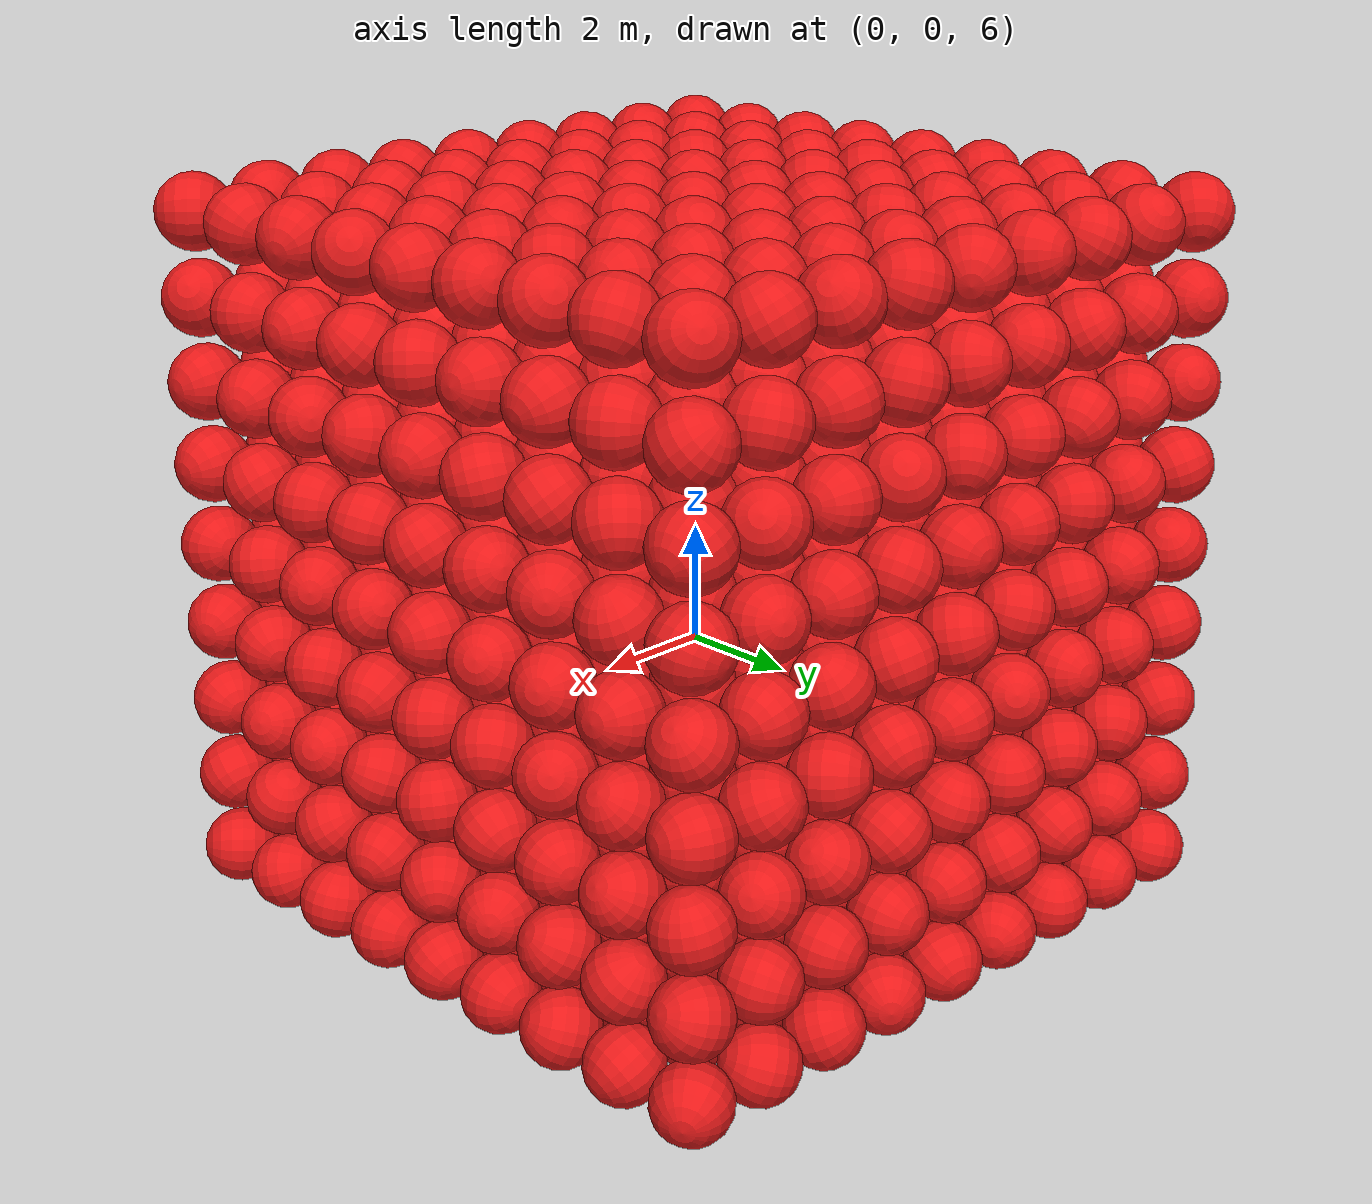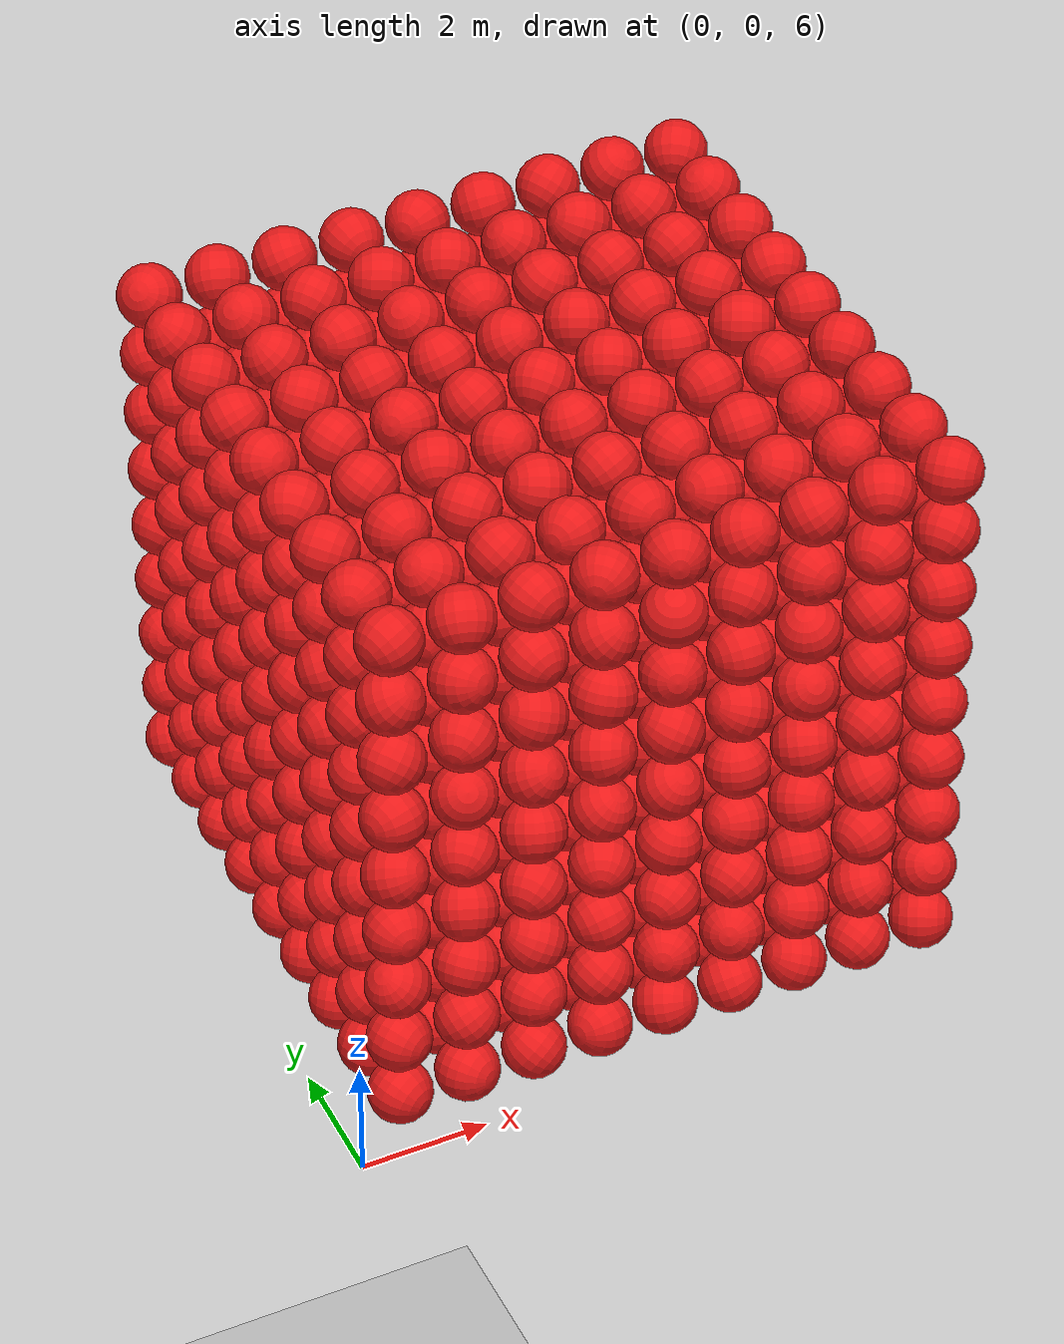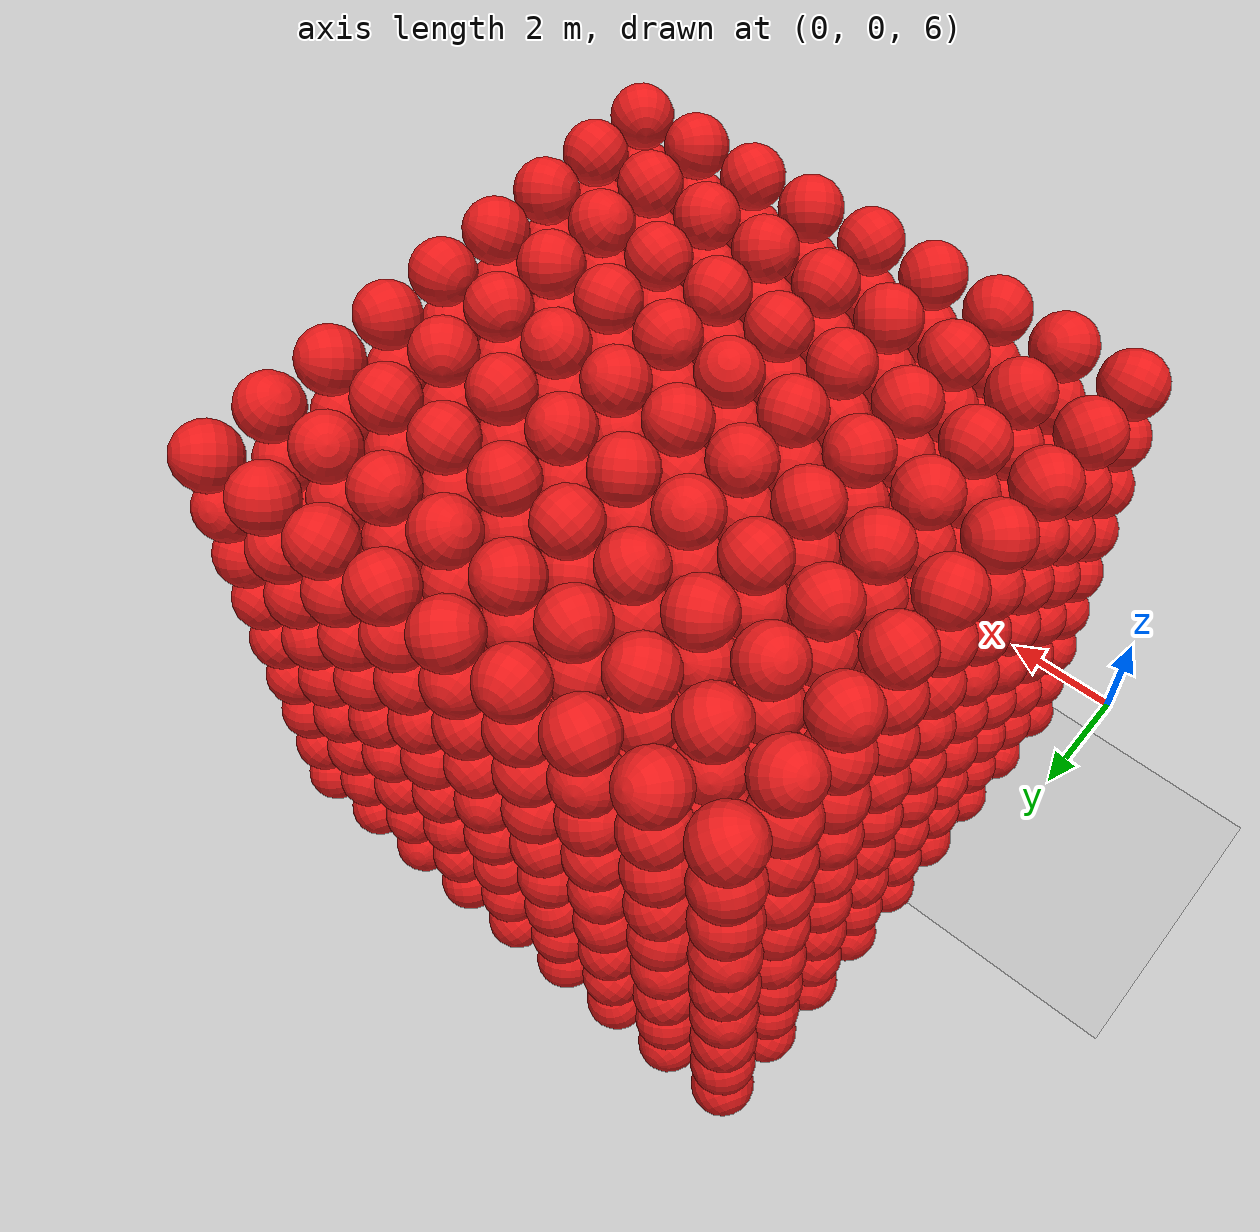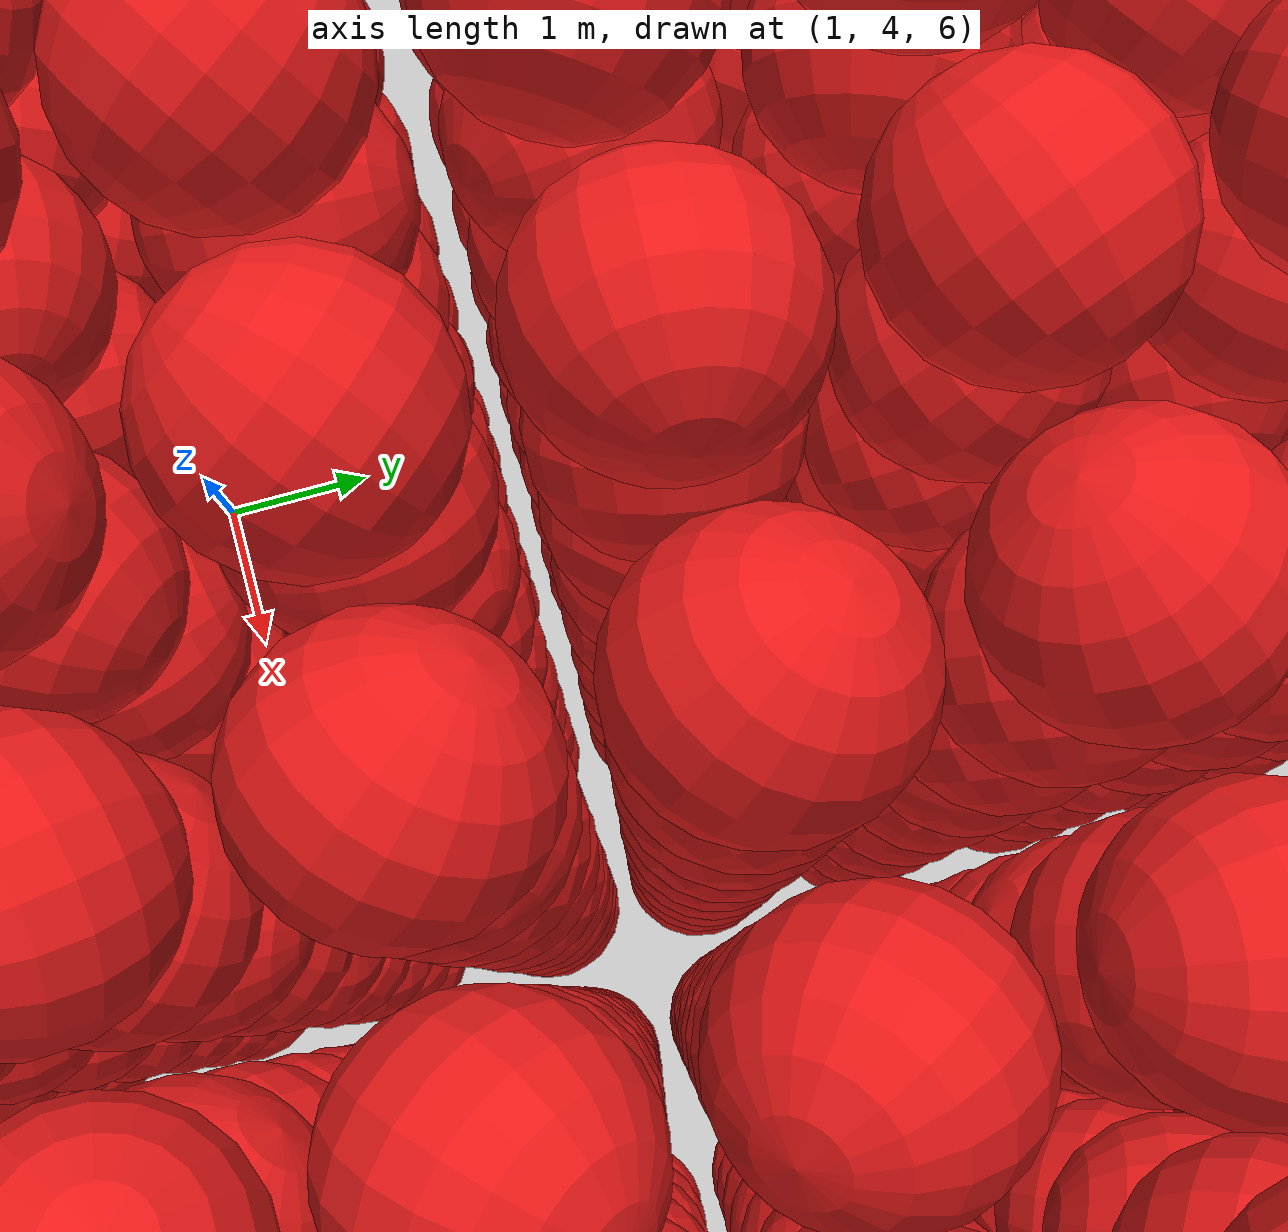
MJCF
<mujoco model="Humanoid and 100 objects">
    <compiler angle="degree"/>

    <option timestep="0.01" iterations="50" solver="PGS" jacobian="sparse" cone="elliptic" tolerance="1e-10"/>

    <size njmax="5000" nconmax="2000" nstack="1000000000"/>

    <default>
        <geom solimp=".9 .9 .01"/>

        <default class="object5">
			<geom type="sphere" material="geom" rgba=".9 .1 .1 1" size="0.500000"/>
        </default>
    </default>

    <asset>
        <texture type="skybox" builtin="gradient" width="128" height="128" rgb1=".4 .6 .8" rgb2="0 0 0"/>
        <texture name="texgeom" type="cube" builtin="flat" mark="cross" width="128" height="128"
            rgb1="0.6 0.6 0.6" rgb2="0.6 0.6 0.6" markrgb="1 1 1"/>
        <texture name="texplane" type="2d" builtin="checker" rgb1=".4 .4 .4" rgb2=".6 .6 .6"
            width="512" height="512"/>
        <material name='geom' texture="texgeom" texuniform="true"/>
        <material name='MatPlane' reflectance='0.3' texture="texplane" texrepeat="1 1" texuniform="true"/>
    </asset>

    <visual>
        <quality shadowsize="4096" offsamples="8"/>
        <map znear="0.1" force="0.05"/>
    </visual>

    <statistic extent="4"/>

    <worldbody>
        <light directional="true" diffuse=".8 .8 .8" pos="0 0 10" dir="0 0 -10"/>

        <geom pos="0 0 0" type="plane" size="3 3 .5" rgba=".7 .7 .7 1" material="MatPlane"/>
		<body pos="1.100691 1.100555 6.100008" quat="-0.187517 -0.135960 0.635030 0.736946"> <freejoint/> <geom class="object5"/> </body>
		<body pos="1.100590 1.100142 7.200593" quat="0.512254 -0.162196 -0.654963 -0.531330"> <freejoint/> <geom class="object5"/> </body>
		<body pos="1.100993 1.100481 8.300828" quat="0.176581 0.543642 0.779176 0.257210"> <freejoint/> <geom class="object5"/> </body>
		<body pos="1.100628 1.100647 9.400062" quat="0.672237 0.611670 0.298933 -0.290855"> <freejoint/> <geom class="object5"/> </body>
		<body pos="1.100344 1.100076 10.500520" quat="0.167367 0.349512 -0.769195 -0.508103"> <freejoint/> <geom class="object5"/> </body>
		<body pos="1.100463 1.100362 11.600952" quat="0.558639 0.592084 -0.379319 -0.439859"> <freejoint/> <geom class="object5"/> </body>
		<body pos="1.100572 1.100593 12.700699" quat="-0.420530 -0.229875 -0.353239 -0.803451"> <freejoint/> <geom class="object5"/> </body>
		<body pos="1.100087 1.100549 13.800318" quat="0.838705 0.380530 0.122724 0.369742"> <freejoint/> <geom class="object5"/> </body>
		<body pos="1.100977 1.100427 14.900913" quat="0.565069 0.476773 -0.642908 -0.200136"> <freejoint/> <geom class="object5"/> </body>
		<body pos="1.100296 2.200629 6.100136" quat="-0.191487 0.554575 -0.379657 -0.715290"> <freejoint/> <geom class="object5"/> </body>
		<body pos="1.100999 2.200605 7.200244" quat="-0.240114 0.913348 0.225290 -0.239554"> <freejoint/> <geom class="object5"/> </body>
		<body pos="1.100604 2.200181 8.300809" quat="0.760188 -0.030412 0.607682 -0.227842"> <freejoint/> <geom class="object5"/> </body>
		<body pos="1.100726 2.200154 9.400509" quat="0.277487 -0.573722 -0.722145 -0.268982"> <freejoint/> <geom class="object5"/> </body>
		<body pos="1.100446 2.200758 10.500131" quat="0.787219 -0.548315 -0.238118 -0.151448"> <freejoint/> <geom class="object5"/> </body>
		<body pos="1.100973 2.200177 11.600882" quat="0.115737 -0.403062 0.902831 0.095086"> <freejoint/> <geom class="object5"/> </body>
		<body pos="1.100463 2.200808 12.700361" quat="0.819697 0.096618 0.469573 0.313469"> <freejoint/> <geom class="object5"/> </body>
		<body pos="1.100205 2.200835 13.800865" quat="-0.791530 0.197146 -0.391415 0.425921"> <freejoint/> <geom class="object5"/> </body>
		<body pos="1.100488 2.200792 14.900524" quat="0.253904 -0.728996 -0.354072 -0.527949"> <freejoint/> <geom class="object5"/> </body>
		<body pos="1.100852 3.300974 6.100624" quat="0.556973 0.682804 0.208687 0.424274"> <freejoint/> <geom class="object5"/> </body>
		<body pos="1.100405 3.300482 7.200064" quat="0.438240 -0.215452 0.505285 0.711487"> <freejoint/> <geom class="object5"/> </body>
		<body pos="1.100484 3.300356 8.300054" quat="0.626791 0.310263 -0.093723 0.708580"> <freejoint/> <geom class="object5"/> </body>
		<body pos="1.100724 3.300657 9.400515" quat="0.618086 -0.720981 -0.046755 -0.309790"> <freejoint/> <geom class="object5"/> </body>
		<body pos="1.100195 3.300151 10.500901" quat="-0.523531 0.558950 0.243742 -0.595046"> <freejoint/> <geom class="object5"/> </body>
		<body pos="1.100005 3.300853 11.600467" quat="0.570583 -0.473413 0.518462 -0.426042"> <freejoint/> <geom class="object5"/> </body>
		<body pos="1.100998 3.300938 12.700554" quat="0.791823 0.259958 0.537406 0.128968"> <freejoint/> <geom class="object5"/> </body>
		<body pos="1.100192 3.300906 13.800515" quat="0.785744 -0.193172 -0.462789 0.362100"> <freejoint/> <geom class="object5"/> </body>
		<body pos="1.100313 3.300118 14.900889" quat="0.332486 0.757345 -0.142607 0.543640"> <freejoint/> <geom class="object5"/> </body>
		<body pos="1.100805 4.400360 6.100914" quat="-0.446146 -0.706042 -0.093024 -0.542038"> <freejoint/> <geom class="object5"/> </body>
		<body pos="1.100002 4.400615 7.200661" quat="0.255013 0.287043 0.557703 -0.735895"> <freejoint/> <geom class="object5"/> </body>
		<body pos="1.100681 4.400571 8.300690" quat="0.602033 -0.354825 -0.656639 -0.283690"> <freejoint/> <geom class="object5"/> </body>
		<body pos="1.100789 4.400498 9.400437" quat="-0.605954 -0.430237 0.336024 0.578622"> <freejoint/> <geom class="object5"/> </body>
		<body pos="1.100706 4.400577 10.500994" quat="-0.140122 -0.024000 -0.816178 0.560039"> <freejoint/> <geom class="object5"/> </body>
		<body pos="1.100407 4.400300 11.600605" quat="0.465500 0.752820 0.437060 0.159841"> <freejoint/> <geom class="object5"/> </body>
		<body pos="1.100449 4.400153 12.700211" quat="0.309261 0.704167 0.209111 0.603970"> <freejoint/> <geom class="object5"/> </body>
		<body pos="1.100216 4.400684 13.800315" quat="-0.670191 0.452217 -0.095077 -0.580779"> <freejoint/> <geom class="object5"/> </body>
		<body pos="1.100935 4.400391 14.900588" quat="-0.786455 0.464215 -0.403461 -0.056680"> <freejoint/> <geom class="object5"/> </body>
		<body pos="1.100402 5.500334 6.100268" quat="0.367455 -0.356172 0.632829 0.581073"> <freejoint/> <geom class="object5"/> </body>
		<body pos="1.100274 5.500223 7.200252" quat="-0.513030 -0.528070 -0.145488 0.660891"> <freejoint/> <geom class="object5"/> </body>
		<body pos="1.100617 5.500194 8.300808" quat="0.653476 -0.472845 0.475043 -0.351741"> <freejoint/> <geom class="object5"/> </body>
		<body pos="1.100417 5.500322 9.400434" quat="-0.265349 -0.616616 0.263194 -0.692895"> <freejoint/> <geom class="object5"/> </body>
		<body pos="1.100201 5.500499 10.500275" quat="-0.132410 0.159744 -0.742545 0.636849"> <freejoint/> <geom class="object5"/> </body>
		<body pos="1.100858 5.500085 11.600177" quat="-0.816549 0.151001 0.348806 0.434489"> <freejoint/> <geom class="object5"/> </body>
		<body pos="1.100214 5.500966 12.700484" quat="-0.641112 -0.471151 -0.236992 0.557518"> <freejoint/> <geom class="object5"/> </body>
		<body pos="1.100043 5.500355 13.800641" quat="0.422971 -0.587438 0.375166 -0.579018"> <freejoint/> <geom class="object5"/> </body>
		<body pos="1.100296 5.500272 14.900913" quat="0.226116 0.004754 0.507259 -0.831587"> <freejoint/> <geom class="object5"/> </body>
		<body pos="1.100884 6.600530 6.100005" quat="-0.522742 -0.368526 -0.715007 0.282301"> <freejoint/> <geom class="object5"/> </body>
		<body pos="1.100028 6.600500 7.200481" quat="-0.419452 0.171385 -0.402621 0.795351"> <freejoint/> <geom class="object5"/> </body>
		<body pos="1.100006 6.600565 8.300369" quat="-0.241454 -0.898711 0.351467 0.102415"> <freejoint/> <geom class="object5"/> </body>
		<body pos="1.100765 6.600791 9.400247" quat="-0.551408 -0.244412 0.403319 -0.688146"> <freejoint/> <geom class="object5"/> </body>
		<body pos="1.100430 6.600016 10.500071" quat="0.305429 0.439974 0.595732 0.598531"> <freejoint/> <geom class="object5"/> </body>
		<body pos="1.100630 6.600131 11.600062" quat="0.614477 0.536114 0.278805 0.507216"> <freejoint/> <geom class="object5"/> </body>
		<body pos="1.100203 6.600795 12.700975" quat="-0.252549 -0.804175 -0.062865 0.534386"> <freejoint/> <geom class="object5"/> </body>
		<body pos="1.100852 6.600945 13.800129" quat="0.275852 -0.589054 -0.556119 -0.517352"> <freejoint/> <geom class="object5"/> </body>
		<body pos="1.100515 6.600482 14.900446" quat="0.866074 0.084053 0.490417 -0.048397"> <freejoint/> <geom class="object5"/> </body>
		<body pos="1.100333 7.700259 6.100974" quat="-0.568644 0.699683 -0.007073 -0.432479"> <freejoint/> <geom class="object5"/> </body>
		<body pos="1.100616 7.700007 7.200063" quat="0.532388 0.514819 0.420229 0.524339"> <freejoint/> <geom class="object5"/> </body>
		<body pos="1.100679 7.700777 8.300694" quat="-0.462211 -0.073077 0.443399 -0.764473"> <freejoint/> <geom class="object5"/> </body>
		<body pos="1.100556 7.700433 9.400058" quat="-0.132789 0.776948 0.270557 0.552737"> <freejoint/> <geom class="object5"/> </body>
		<body pos="1.100936 7.700325 10.500746" quat="0.911752 -0.163119 0.052714 0.373258"> <freejoint/> <geom class="object5"/> </body>
		<body pos="1.100469 7.700183 11.600226" quat="-0.124856 -0.687363 0.355475 -0.620951"> <freejoint/> <geom class="object5"/> </body>
		<body pos="1.100432 7.700543 12.700610" quat="-0.099783 -0.655558 -0.338071 -0.667829"> <freejoint/> <geom class="object5"/> </body>
		<body pos="1.100730 7.700346 13.800652" quat="-0.040623 -0.261444 -0.385496 -0.883963"> <freejoint/> <geom class="object5"/> </body>
		<body pos="1.100370 7.700377 14.900482" quat="0.595390 0.385475 0.704491 0.024738"> <freejoint/> <geom class="object5"/> </body>
		<body pos="1.100855 8.800465 6.100265" quat="0.704530 0.341340 0.223934 -0.580498"> <freejoint/> <geom class="object5"/> </body>
		<body pos="1.100420 8.800137 7.200292" quat="-0.638473 0.560749 0.141591 0.507803"> <freejoint/> <geom class="object5"/> </body>
		<body pos="1.100421 8.800400 8.300554" quat="0.247119 0.016119 0.223886 -0.942628"> <freejoint/> <geom class="object5"/> </body>
		<body pos="1.100762 8.800651 9.400351" quat="-0.385476 -0.464351 -0.720891 -0.340739"> <freejoint/> <geom class="object5"/> </body>
		<body pos="1.100833 8.800234 10.500069" quat="-0.009330 -0.668590 -0.172308 -0.723332"> <freejoint/> <geom class="object5"/> </body>
		<body pos="1.100721 8.800342 11.600566" quat="0.433515 0.427872 0.563543 -0.558041"> <freejoint/> <geom class="object5"/> </body>
		<body pos="1.100085 8.800633 12.700266" quat="0.758237 -0.384129 0.413604 -0.326272"> <freejoint/> <geom class="object5"/> </body>
		<body pos="1.100365 8.800592 13.800905" quat="-0.314566 0.600923 0.318918 -0.661991"> <freejoint/> <geom class="object5"/> </body>
		<body pos="1.100851 8.800696 14.900562" quat="-0.334989 -0.345139 -0.872498 -0.086076"> <freejoint/> <geom class="object5"/> </body>
		<body pos="1.100657 9.900572 6.100402" quat="0.547825 -0.175760 0.564225 -0.592154"> <freejoint/> <geom class="object5"/> </body>
		<body pos="1.100441 9.900701 7.200703" quat="0.025084 0.276944 0.607877 0.743746"> <freejoint/> <geom class="object5"/> </body>
		<body pos="1.100337 9.900564 8.300855" quat="0.218363 0.020184 0.865606 0.450151"> <freejoint/> <geom class="object5"/> </body>
		<body pos="1.100106 9.900502 9.400019" quat="-0.075710 0.537151 -0.600678 0.587301"> <freejoint/> <geom class="object5"/> </body>
		<body pos="1.100180 9.900370 10.500205" quat="-0.658767 -0.109561 -0.362340 -0.650179"> <freejoint/> <geom class="object5"/> </body>
		<body pos="1.100499 9.900239 11.600350" quat="0.368387 0.303923 -0.497778 -0.723975"> <freejoint/> <geom class="object5"/> </body>
		<body pos="1.100381 9.900281 12.700180" quat="-0.563461 -0.732165 0.382611 0.007491"> <freejoint/> <geom class="object5"/> </body>
		<body pos="1.100722 9.900761 13.800269" quat="-0.533121 -0.758414 -0.129854 0.351751"> <freejoint/> <geom class="object5"/> </body>
		<body pos="1.100977 9.900552 14.900044" quat="0.332997 -0.898372 0.171038 -0.229753"> <freejoint/> <geom class="object5"/> </body>
		<body pos="2.200117 1.100380 6.100765" quat="0.552495 0.254477 0.621504 -0.493684"> <freejoint/> <geom class="object5"/> </body>
		<body pos="2.200646 1.100387 7.200562" quat="-0.783135 -0.275386 -0.414759 -0.372609"> <freejoint/> <geom class="object5"/> </body>
		<body pos="2.200373 1.100115 8.300501" quat="0.608962 -0.300708 -0.002813 -0.733984"> <freejoint/> <geom class="object5"/> </body>
		<body pos="2.200576 1.100515 9.400355" quat="0.762944 -0.327530 -0.090539 -0.549949"> <freejoint/> <geom class="object5"/> </body>
		<body pos="2.200771 1.100273 10.500525" quat="0.042516 0.510221 0.597988 -0.616667"> <freejoint/> <geom class="object5"/> </body>
		<body pos="2.200979 1.100632 11.600073" quat="-0.689480 -0.335229 -0.175420 0.617630"> <freejoint/> <geom class="object5"/> </body>
		<body pos="2.200916 1.100630 12.700956" quat="0.475203 0.048637 0.652144 0.588664"> <freejoint/> <geom class="object5"/> </body>
		<body pos="2.200132 1.100761 13.800617" quat="-0.144296 0.481123 -0.650873 -0.569266"> <freejoint/> <geom class="object5"/> </body>
		<body pos="2.200948 1.100396 14.900532" quat="0.781059 -0.309536 0.317142 0.439950"> <freejoint/> <geom class="object5"/> </body>
		<body pos="2.200223 2.200555 6.100455" quat="0.449383 0.179281 0.074811 -0.871961"> <freejoint/> <geom class="object5"/> </body>
		<body pos="2.200879 2.200937 7.200806" quat="0.748199 0.038655 -0.617481 0.239627"> <freejoint/> <geom class="object5"/> </body>
		<body pos="2.200191 2.200857 8.300943" quat="-0.734471 -0.377023 0.553852 -0.107952"> <freejoint/> <geom class="object5"/> </body>
		<body pos="2.200493 2.200030 9.400573" quat="0.127030 0.423699 -0.742234 0.503419"> <freejoint/> <geom class="object5"/> </body>
		<body pos="2.200193 2.200531 10.500924" quat="0.646868 0.632544 -0.259823 0.337554"> <freejoint/> <geom class="object5"/> </body>
		<body pos="2.200206 2.200861 11.600658" quat="-0.563427 0.113969 0.656474 0.488470"> <freejoint/> <geom class="object5"/> </body>
		<body pos="2.200753 2.200703 12.700247" quat="-0.668232 -0.055030 -0.555762 -0.491495"> <freejoint/> <geom class="object5"/> </body>
		<body pos="2.200420 2.200666 13.800973" quat="-0.374525 0.053358 0.732041 -0.566568"> <freejoint/> <geom class="object5"/> </body>
		<body pos="2.200789 2.200103 14.900884" quat="0.038114 0.812622 0.438946 0.381471"> <freejoint/> <geom class="object5"/> </body>
		<body pos="2.200003 3.300206 6.100260" quat="-0.699641 0.391970 0.537417 -0.260854"> <freejoint/> <geom class="object5"/> </body>
		<body pos="2.200136 3.300666 7.200830" quat="0.381949 -0.793154 -0.266569 0.392381"> <freejoint/> <geom class="object5"/> </body>
		<body pos="2.200516 3.300978 8.300268" quat="0.542904 -0.186800 -0.537665 -0.617476"> <freejoint/> <geom class="object5"/> </body>
		<body pos="2.200739 3.300372 9.400381" quat="-0.527999 -0.548413 -0.641059 -0.097485"> <freejoint/> <geom class="object5"/> </body>
		<body pos="2.200988 3.300385 10.500943" quat="-0.478965 0.611300 0.365823 0.512911"> <freejoint/> <geom class="object5"/> </body>
		<body pos="2.200602 3.300107 11.600455" quat="0.220159 -0.630139 -0.681793 -0.299354"> <freejoint/> <geom class="object5"/> </body>
		<body pos="2.200931 3.300514 12.700875" quat="-0.216150 0.681802 0.061660 0.696149"> <freejoint/> <geom class="object5"/> </body>
		<body pos="2.200103 3.300212 13.800702" quat="-0.247602 -0.890417 -0.206604 -0.321192"> <freejoint/> <geom class="object5"/> </body>
		<body pos="2.200393 3.300181 14.900209" quat="0.167667 0.168994 -0.585927 0.774609"> <freejoint/> <geom class="object5"/> </body>
		<body pos="2.200056 4.400202 6.100508" quat="0.418095 -0.570893 0.695290 -0.125892"> <freejoint/> <geom class="object5"/> </body>
		<body pos="2.200056 4.400674 7.200280" quat="0.488972 0.808021 0.328635 -0.002754"> <freejoint/> <geom class="object5"/> </body>
		<body pos="2.200099 4.400288 8.300538" quat="-0.771181 -0.342700 0.141354 -0.517548"> <freejoint/> <geom class="object5"/> </body>
		<body pos="2.200170 4.400676 9.400570" quat="0.099727 0.902191 0.247862 -0.338630"> <freejoint/> <geom class="object5"/> </body>
		<body pos="2.200521 4.400865 10.500994" quat="0.539839 -0.243379 0.397772 0.700798"> <freejoint/> <geom class="object5"/> </body>
		<body pos="2.200668 4.400481 11.600286" quat="0.190175 -0.326951 0.918441 -0.115767"> <freejoint/> <geom class="object5"/> </body>
		<body pos="2.200962 4.400676 12.700706" quat="0.575167 0.552779 0.419422 -0.433247"> <freejoint/> <geom class="object5"/> </body>
		<body pos="2.200830 4.400464 13.800299" quat="0.056568 0.804952 0.094984 -0.582950"> <freejoint/> <geom class="object5"/> </body>
		<body pos="2.200354 4.400187 14.900351" quat="-0.456013 0.493357 -0.170261 -0.720876"> <freejoint/> <geom class="object5"/> </body>
		<body pos="2.200309 5.500837 6.100281" quat="0.628224 0.070370 -0.772789 0.056390"> <freejoint/> <geom class="object5"/> </body>
		<body pos="2.200283 5.500715 7.200734" quat="-0.093836 -0.592337 -0.679042 -0.423360"> <freejoint/> <geom class="object5"/> </body>
		<body pos="2.200636 5.500806 8.300668" quat="-0.407109 -0.682090 -0.484777 0.366069"> <freejoint/> <geom class="object5"/> </body>
		<body pos="2.200072 5.500499 9.400986" quat="0.737371 0.136962 0.485359 0.449392"> <freejoint/> <geom class="object5"/> </body>
		<body pos="2.200695 5.500677 10.500282" quat="0.137628 0.199835 0.528266 -0.813670"> <freejoint/> <geom class="object5"/> </body>
		<body pos="2.200214 5.500988 11.600817" quat="0.299745 0.413364 0.699464 -0.500033"> <freejoint/> <geom class="object5"/> </body>
		<body pos="2.200665 5.500029 12.700544" quat="0.044499 0.573192 -0.479844 0.662737"> <freejoint/> <geom class="object5"/> </body>
		<body pos="2.200976 5.500331 13.800624" quat="0.121169 -0.183219 -0.633294 -0.742083"> <freejoint/> <geom class="object5"/> </body>
		<body pos="2.200083 5.500390 14.900239" quat="-0.026019 0.379240 -0.687487 0.618758"> <freejoint/> <geom class="object5"/> </body>
		<body pos="2.200930 6.600829 6.100485" quat="0.318930 -0.087032 -0.162765 -0.929633"> <freejoint/> <geom class="object5"/> </body>
		<body pos="2.200927 6.600043 7.200476" quat="-0.175385 0.052282 0.764722 0.617825"> <freejoint/> <geom class="object5"/> </body>
		<body pos="2.200015 6.600781 8.300485" quat="-0.154484 0.454657 0.526886 0.701294"> <freejoint/> <geom class="object5"/> </body>
		<body pos="2.200196 6.600870 9.400307" quat="-0.245478 0.874846 -0.364345 -0.204053"> <freejoint/> <geom class="object5"/> </body>
		<body pos="2.200091 6.600667 10.500731" quat="-0.333598 -0.271329 0.392453 0.813064"> <freejoint/> <geom class="object5"/> </body>
		<body pos="2.200699 6.600090 11.600471" quat="0.304211 0.056790 -0.806045 -0.504501"> <freejoint/> <geom class="object5"/> </body>
		<body pos="2.200987 6.600795 12.700933" quat="-0.377856 -0.724841 0.449472 -0.360285"> <freejoint/> <geom class="object5"/> </body>
		<body pos="2.200438 6.600909 13.800834" quat="-0.277163 0.597060 -0.534187 -0.530419"> <freejoint/> <geom class="object5"/> </body>
		<body pos="2.200297 6.600025 14.900918" quat="0.427165 -0.610154 -0.006079 0.667237"> <freejoint/> <geom class="object5"/> </body>
		<body pos="2.200380 7.700219 6.100723" quat="0.617970 0.437788 0.271065 0.594120"> <freejoint/> <geom class="object5"/> </body>
		<body pos="2.200511 7.700329 7.200001" quat="0.140479 -0.571646 -0.531461 -0.609127"> <freejoint/> <geom class="object5"/> </body>
		<body pos="2.200505 7.700017 8.300471" quat="-0.792861 -0.100845 -0.587657 0.125936"> <freejoint/> <geom class="object5"/> </body>
		<body pos="2.200818 7.700085 9.400233" quat="-0.514653 -0.300064 -0.184246 -0.781759"> <freejoint/> <geom class="object5"/> </body>
		<body pos="2.200407 7.700676 10.500543" quat="-0.308692 0.349145 0.386113 -0.796068"> <freejoint/> <geom class="object5"/> </body>
		<body pos="2.200440 7.700937 11.600570" quat="0.184201 0.627775 -0.600363 0.459927"> <freejoint/> <geom class="object5"/> </body>
		<body pos="2.200295 7.700571 12.700635" quat="-0.196260 -0.487437 0.845015 -0.099185"> <freejoint/> <geom class="object5"/> </body>
		<body pos="2.200532 7.700635 13.800668" quat="-0.106325 -0.570114 0.338892 0.740822"> <freejoint/> <geom class="object5"/> </body>
		<body pos="2.200371 7.700639 14.900890" quat="-0.041236 0.313829 -0.084569 -0.944806"> <freejoint/> <geom class="object5"/> </body>
		<body pos="2.200113 8.800108 6.100446" quat="0.573184 0.174777 0.561200 -0.570936"> <freejoint/> <geom class="object5"/> </body>
		<body pos="2.200307 8.800950 7.200010" quat="-0.608344 0.467509 0.611365 0.193874"> <freejoint/> <geom class="object5"/> </body>
		<body pos="2.200518 8.800943 8.300741" quat="0.297944 0.362606 0.553908 0.687701"> <freejoint/> <geom class="object5"/> </body>
		<body pos="2.200982 8.800919 9.400283" quat="-0.561978 0.408705 -0.408047 -0.592147"> <freejoint/> <geom class="object5"/> </body>
		<body pos="2.200771 8.800541 10.500332" quat="0.196497 0.890600 0.357677 -0.200717"> <freejoint/> <geom class="object5"/> </body>
		<body pos="2.200546 8.800182 11.600236" quat="-0.490638 -0.400246 0.737212 0.235788"> <freejoint/> <geom class="object5"/> </body>
		<body pos="2.200829 8.800389 12.700168" quat="0.424037 0.658340 -0.255136 -0.567174"> <freejoint/> <geom class="object5"/> </body>
		<body pos="2.200996 8.800959 13.800156" quat="0.679426 -0.119473 -0.438630 -0.575943"> <freejoint/> <geom class="object5"/> </body>
		<body pos="2.200260 8.800544 14.900082" quat="0.191933 -0.920893 -0.088196 -0.327626"> <freejoint/> <geom class="object5"/> </body>
		<body pos="2.200944 9.900303 6.100428" quat="0.278160 -0.205401 -0.628457 -0.696763"> <freejoint/> <geom class="object5"/> </body>
		<body pos="2.200305 9.900824 7.200627" quat="-0.446747 0.729497 -0.094533 0.509229"> <freejoint/> <geom class="object5"/> </body>
		<body pos="2.200539 9.900025 8.300007" quat="0.559830 -0.102945 -0.413411 0.710692"> <freejoint/> <geom class="object5"/> </body>
		<body pos="2.200656 9.900285 9.400645" quat="-0.556730 -0.765846 -0.309381 0.088406"> <freejoint/> <geom class="object5"/> </body>
		<body pos="2.200926 9.900749 10.500148" quat="-0.647356 -0.485715 0.542929 0.224143"> <freejoint/> <geom class="object5"/> </body>
		<body pos="2.200114 9.900960 11.600119" quat="-0.016362 -0.299192 -0.064719 -0.951855"> <freejoint/> <geom class="object5"/> </body>
		<body pos="2.200330 9.900265 12.700246" quat="0.577334 -0.602974 0.523782 -0.169589"> <freejoint/> <geom class="object5"/> </body>
		<body pos="2.200663 9.900954 13.800094" quat="0.422063 -0.199420 -0.884165 -0.018596"> <freejoint/> <geom class="object5"/> </body>
		<body pos="2.200462 9.900877 14.900660" quat="-0.441488 0.312508 0.289138 0.789827"> <freejoint/> <geom class="object5"/> </body>
		<body pos="3.300882 1.100335 6.100427" quat="0.476868 0.664199 0.575705 -0.000549"> <freejoint/> <geom class="object5"/> </body>
		<body pos="3.300584 1.100925 7.200166" quat="-0.207214 -0.396801 0.545052 -0.708894"> <freejoint/> <geom class="object5"/> </body>
		<body pos="3.300281 1.100555 8.300619" quat="-0.305259 -0.817421 -0.281711 -0.399096"> <freejoint/> <geom class="object5"/> </body>
		<body pos="3.300096 1.100131 9.400610" quat="0.370374 0.808584 -0.000432 -0.457181"> <freejoint/> <geom class="object5"/> </body>
		<body pos="3.300170 1.100049 10.500226" quat="-0.410778 0.209502 0.215273 0.860830"> <freejoint/> <geom class="object5"/> </body>
		<body pos="3.300590 1.100111 11.600641" quat="-0.775336 -0.243036 -0.385325 0.437393"> <freejoint/> <geom class="object5"/> </body>
		<body pos="3.300067 1.100757 12.700241" quat="-0.369590 -0.670275 -0.504789 -0.399152"> <freejoint/> <geom class="object5"/> </body>
		<body pos="3.300214 1.100906 13.800278" quat="-0.757261 0.531573 0.314862 0.211772"> <freejoint/> <geom class="object5"/> </body>
		<body pos="3.300344 1.100690 14.900234" quat="-0.467105 -0.347218 -0.689334 0.431360"> <freejoint/> <geom class="object5"/> </body>
		<body pos="3.300736 2.200010 6.100356" quat="-0.449839 0.739699 0.454928 -0.208642"> <freejoint/> <geom class="object5"/> </body>
		<body pos="3.300686 2.200699 7.200590" quat="0.682116 0.415341 0.056729 -0.599159"> <freejoint/> <geom class="object5"/> </body>
		<body pos="3.300886 2.200257 8.300464" quat="-0.320817 0.486859 0.574221 0.574730"> <freejoint/> <geom class="object5"/> </body>
		<body pos="3.300877 2.200087 9.400668" quat="0.010161 -0.689889 0.371554 -0.621207"> <freejoint/> <geom class="object5"/> </body>
		<body pos="3.300207 2.200262 10.500099" quat="-0.657459 -0.336268 0.177338 -0.650555"> <freejoint/> <geom class="object5"/> </body>
		<body pos="3.300063 2.200008 11.600774" quat="0.312401 -0.651241 0.376253 -0.580280"> <freejoint/> <geom class="object5"/> </body>
		<body pos="3.300120 2.200681 12.700145" quat="-0.543918 -0.449060 -0.596871 -0.382418"> <freejoint/> <geom class="object5"/> </body>
		<body pos="3.300071 2.200038 13.800308" quat="0.030833 -0.208660 0.970311 -0.118351"> <freejoint/> <geom class="object5"/> </body>
		<body pos="3.300151 2.200778 14.900741" quat="-0.874176 -0.062696 -0.439192 -0.197473"> <freejoint/> <geom class="object5"/> </body>
		<body pos="3.300430 3.300871 6.100707" quat="-0.660496 -0.646507 -0.357655 0.133629"> <freejoint/> <geom class="object5"/> </body>
		<body pos="3.300926 3.300334 7.200443" quat="-0.691662 0.371230 0.382423 0.487386"> <freejoint/> <geom class="object5"/> </body>
		<body pos="3.300942 3.300048 8.300800" quat="-0.056970 -0.378857 -0.780973 0.493257"> <freejoint/> <geom class="object5"/> </body>
		<body pos="3.300899 3.300776 9.400837" quat="-0.353482 -0.701623 -0.276192 -0.553619"> <freejoint/> <geom class="object5"/> </body>
		<body pos="3.300021 3.300293 10.500240" quat="-0.590108 -0.301153 0.073710 -0.745417"> <freejoint/> <geom class="object5"/> </body>
		<body pos="3.300193 3.300489 11.600407" quat="0.391164 -0.333179 0.511414 0.688795"> <freejoint/> <geom class="object5"/> </body>
		<body pos="3.300765 3.300334 12.700719" quat="-0.610707 0.151396 -0.507800 -0.588435"> <freejoint/> <geom class="object5"/> </body>
		<body pos="3.300055 3.300026 13.800955" quat="0.069545 0.706803 0.247738 0.658953"> <freejoint/> <geom class="object5"/> </body>
		<body pos="3.300319 3.300848 14.900494" quat="-0.718120 0.582216 0.311044 -0.220409"> <freejoint/> <geom class="object5"/> </body>
		<body pos="3.300719 4.400419 6.100056" quat="0.337882 -0.799679 -0.359497 0.342215"> <freejoint/> <geom class="object5"/> </body>
		<body pos="3.300316 4.400147 7.200992" quat="-0.518325 -0.218872 -0.610149 0.557810"> <freejoint/> <geom class="object5"/> </body>
		<body pos="3.300373 4.400989 8.300543" quat="0.148182 -0.730424 -0.665838 -0.034387"> <freejoint/> <geom class="object5"/> </body>
		<body pos="3.300220 4.400937 9.400278" quat="0.607677 0.422370 -0.201710 -0.641596"> <freejoint/> <geom class="object5"/> </body>
		<body pos="3.300341 4.400384 10.500093" quat="0.716605 -0.473338 -0.512165 0.010738"> <freejoint/> <geom class="object5"/> </body>
		<body pos="3.300508 4.400051 11.600367" quat="0.156233 0.911541 -0.119515 0.361111"> <freejoint/> <geom class="object5"/> </body>
		<body pos="3.300016 4.400153 12.700900" quat="-0.670056 -0.695240 0.109963 -0.235742"> <freejoint/> <geom class="object5"/> </body>
		<body pos="3.300219 4.400904 13.800683" quat="-0.300782 -0.231722 -0.691378 -0.614680"> <freejoint/> <geom class="object5"/> </body>
		<body pos="3.300884 4.400921 14.900782" quat="-0.469971 0.152229 -0.542921 -0.679110"> <freejoint/> <geom class="object5"/> </body>
		<body pos="3.300688 5.500911 6.100751" quat="0.723374 -0.615778 -0.253709 -0.182152"> <freejoint/> <geom class="object5"/> </body>
		<body pos="3.300936 5.500106 7.200531" quat="0.300475 -0.544608 -0.749349 -0.227140"> <freejoint/> <geom class="object5"/> </body>
		<body pos="3.300363 5.500162 8.300894" quat="-0.173845 0.497409 -0.845731 -0.084271"> <freejoint/> <geom class="object5"/> </body>
		<body pos="3.300050 5.500496 9.400270" quat="0.553738 0.745622 -0.325790 0.176869"> <freejoint/> <geom class="object5"/> </body>
		<body pos="3.300732 5.500612 10.500581" quat="-0.657471 -0.192548 -0.714146 -0.143709"> <freejoint/> <geom class="object5"/> </body>
		<body pos="3.300658 5.500575 11.600976" quat="-0.104022 0.495215 0.123802 -0.853589"> <freejoint/> <geom class="object5"/> </body>
		<body pos="3.300512 5.500408 12.700220" quat="-0.504464 -0.115009 0.785864 -0.338685"> <freejoint/> <geom class="object5"/> </body>
		<body pos="3.300284 5.500364 13.800499" quat="0.474599 -0.401421 -0.723176 -0.301054"> <freejoint/> <geom class="object5"/> </body>
		<body pos="3.300298 5.500826 14.900136" quat="0.461839 0.530118 0.077724 -0.706851"> <freejoint/> <geom class="object5"/> </body>
		<body pos="3.300508 6.600714 6.100698" quat="0.497395 0.254332 0.552810 -0.618315"> <freejoint/> <geom class="object5"/> </body>
		<body pos="3.300820 6.600034 7.200516" quat="0.399765 0.662564 -0.573595 0.268676"> <freejoint/> <geom class="object5"/> </body>
		<body pos="3.300889 6.600643 8.300786" quat="-0.020051 -0.218507 0.854297 0.471200"> <freejoint/> <geom class="object5"/> </body>
		<body pos="3.300826 6.600011 9.400096" quat="0.084852 0.698306 -0.461942 0.540165"> <freejoint/> <geom class="object5"/> </body>
		<body pos="3.300638 6.600725 10.500895" quat="0.384274 -0.420361 -0.654870 -0.496765"> <freejoint/> <geom class="object5"/> </body>
		<body pos="3.300718 6.600129 11.600221" quat="-0.112081 -0.083841 -0.990023 0.016242"> <freejoint/> <geom class="object5"/> </body>
		<body pos="3.300077 6.600167 12.700748" quat="-0.261760 -0.308458 0.504553 0.762733"> <freejoint/> <geom class="object5"/> </body>
		<body pos="3.300969 6.600577 13.800233" quat="-0.505675 0.422644 0.179353 -0.730409"> <freejoint/> <geom class="object5"/> </body>
		<body pos="3.300958 6.600336 14.900150" quat="-0.294895 -0.664829 0.467240 0.502720"> <freejoint/> <geom class="object5"/> </body>
		<body pos="3.300587 7.700079 6.100193" quat="0.468023 -0.249146 0.576007 -0.622171"> <freejoint/> <geom class="object5"/> </body>
		<body pos="3.300698 7.700190 7.200397" quat="-0.277884 0.729323 0.583887 0.223483"> <freejoint/> <geom class="object5"/> </body>
		<body pos="3.300865 7.700216 8.300065" quat="0.584026 0.115231 0.056923 -0.801496"> <freejoint/> <geom class="object5"/> </body>
		<body pos="3.300853 7.700823 9.400017" quat="-0.044563 0.782567 -0.072913 0.616675"> <freejoint/> <geom class="object5"/> </body>
		<body pos="3.300536 7.700434 10.500024" quat="0.007322 0.632265 0.685611 -0.360728"> <freejoint/> <geom class="object5"/> </body>
		<body pos="3.300133 7.700000 11.600318" quat="0.054078 0.591241 0.311777 0.741825"> <freejoint/> <geom class="object5"/> </body>
		<body pos="3.300756 7.700169 12.700964" quat="-0.320761 0.208200 0.489155 0.783895"> <freejoint/> <geom class="object5"/> </body>
		<body pos="3.300333 7.700463 13.800167" quat="-0.083732 -0.108691 -0.927176 0.348597"> <freejoint/> <geom class="object5"/> </body>
		<body pos="3.300896 7.700427 14.900176" quat="-0.253564 -0.545526 -0.543752 -0.585184"> <freejoint/> <geom class="object5"/> </body>
		<body pos="3.300550 8.800563 6.100305" quat="0.474475 0.318981 0.819974 -0.027676"> <freejoint/> <geom class="object5"/> </body>
		<body pos="3.300518 8.800789 7.200571" quat="0.454919 0.717243 -0.494520 0.184556"> <freejoint/> <geom class="object5"/> </body>
		<body pos="3.300466 8.800617 8.300203" quat="0.248434 -0.675198 -0.382432 0.579771"> <freejoint/> <geom class="object5"/> </body>
		<body pos="3.300768 8.800533 9.400068" quat="-0.370792 -0.602299 0.575873 0.410023"> <freejoint/> <geom class="object5"/> </body>
		<body pos="3.300445 8.800990 10.500794" quat="-0.019855 -0.644007 -0.501658 0.577236"> <freejoint/> <geom class="object5"/> </body>
		<body pos="3.300324 8.800739 11.600160" quat="0.348238 -0.671448 0.322540 -0.569083"> <freejoint/> <geom class="object5"/> </body>
		<body pos="3.300984 8.800593 12.700270" quat="-0.110299 0.698349 0.012791 -0.707092"> <freejoint/> <geom class="object5"/> </body>
		<body pos="3.300659 8.800449 13.800147" quat="0.431454 0.049007 -0.646026 0.627771"> <freejoint/> <geom class="object5"/> </body>
		<body pos="3.300868 8.800056 14.900640" quat="0.860615 -0.336665 0.368596 -0.100682"> <freejoint/> <geom class="object5"/> </body>
		<body pos="3.300447 9.900017 6.100861" quat="0.660145 -0.032004 0.105291 0.743033"> <freejoint/> <geom class="object5"/> </body>
		<body pos="3.300404 9.900220 7.200866" quat="0.268875 -0.467317 -0.698387 -0.470720"> <freejoint/> <geom class="object5"/> </body>
		<body pos="3.300206 9.900902 8.300709" quat="-0.825753 -0.167801 0.362201 -0.398478"> <freejoint/> <geom class="object5"/> </body>
		<body pos="3.300597 9.900211 9.400190" quat="-0.589715 0.431333 -0.499988 -0.464974"> <freejoint/> <geom class="object5"/> </body>
		<body pos="3.300482 9.900221 10.500355" quat="0.446433 0.809520 -0.024564 0.380488"> <freejoint/> <geom class="object5"/> </body>
		<body pos="3.300319 9.900302 11.600142" quat="0.496911 -0.305709 0.589975 -0.558167"> <freejoint/> <geom class="object5"/> </body>
		<body pos="3.300614 9.900284 12.700508" quat="0.072800 -0.838675 -0.117824 -0.526727"> <freejoint/> <geom class="object5"/> </body>
		<body pos="3.300918 9.900691 13.800116" quat="-0.443465 -0.612689 -0.624717 0.194112"> <freejoint/> <geom class="object5"/> </body>
		<body pos="3.300796 9.900470 14.900791" quat="-0.151731 0.447416 -0.266132 0.840220"> <freejoint/> <geom class="object5"/> </body>
		<body pos="4.400750 1.100020 6.100755" quat="0.580841 -0.214742 -0.604698 0.500849"> <freejoint/> <geom class="object5"/> </body>
		<body pos="4.400094 1.100550 7.200916" quat="0.044813 -0.912147 -0.120303 0.389239"> <freejoint/> <geom class="object5"/> </body>
		<body pos="4.400261 1.100896 8.300460" quat="-0.456291 -0.517717 0.595423 0.411386"> <freejoint/> <geom class="object5"/> </body>
		<body pos="4.400662 1.100107 9.400836" quat="-0.077339 0.258393 0.693753 -0.667802"> <freejoint/> <geom class="object5"/> </body>
		<body pos="4.400604 1.100016 10.500091" quat="0.799606 0.093860 0.284240 -0.520604"> <freejoint/> <geom class="object5"/> </body>
		<body pos="4.400621 1.100079 11.600646" quat="-0.533057 0.195841 0.774511 0.278621"> <freejoint/> <geom class="object5"/> </body>
		<body pos="4.400332 1.100458 12.700025" quat="0.042158 0.892611 0.407564 -0.188041"> <freejoint/> <geom class="object5"/> </body>
		<body pos="4.400591 1.100573 13.800508" quat="-0.649747 -0.383211 0.002097 -0.656486"> <freejoint/> <geom class="object5"/> </body>
		<body pos="4.400406 1.100593 14.900809" quat="-0.066010 0.390930 0.577407 -0.713735"> <freejoint/> <geom class="object5"/> </body>
		<body pos="4.400620 2.200770 6.100421" quat="-0.138212 -0.025417 -0.641473 0.754164"> <freejoint/> <geom class="object5"/> </body>
		<body pos="4.400502 2.200103 7.200364" quat="0.564062 -0.663149 0.262615 0.416054"> <freejoint/> <geom class="object5"/> </body>
		<body pos="4.400711 2.200105 8.300959" quat="-0.184694 0.145499 -0.971107 -0.040862"> <freejoint/> <geom class="object5"/> </body>
		<body pos="4.400154 2.200308 9.400131" quat="-0.419190 0.436814 0.043404 0.794726"> <freejoint/> <geom class="object5"/> </body>
		<body pos="4.400577 2.200067 10.500248" quat="0.532171 0.507207 0.637812 -0.229631"> <freejoint/> <geom class="object5"/> </body>
		<body pos="4.400987 2.200614 11.600652" quat="0.285260 0.838205 0.310875 -0.345538"> <freejoint/> <geom class="object5"/> </body>
		<body pos="4.400175 2.200060 12.700152" quat="-0.164820 -0.688392 0.657936 -0.257044"> <freejoint/> <geom class="object5"/> </body>
		<body pos="4.400956 2.200029 13.800397" quat="-0.573578 -0.356623 0.723984 -0.140267"> <freejoint/> <geom class="object5"/> </body>
		<body pos="4.400057 2.200048 14.900531" quat="0.450542 0.193596 0.730331 0.475552"> <freejoint/> <geom class="object5"/> </body>
		<body pos="4.400755 3.300326 6.100522" quat="0.420619 0.032471 0.468352 -0.776320"> <freejoint/> <geom class="object5"/> </body>
		<body pos="4.400983 3.300086 7.200413" quat="0.695296 -0.021121 0.160286 -0.700304"> <freejoint/> <geom class="object5"/> </body>
		<body pos="4.400769 3.300742 8.300217" quat="-0.180724 -0.417909 -0.741634 -0.492615"> <freejoint/> <geom class="object5"/> </body>
		<body pos="4.400485 3.300515 9.400839" quat="-0.173964 -0.195951 0.906771 -0.330313"> <freejoint/> <geom class="object5"/> </body>
		<body pos="4.400134 3.300695 10.500923" quat="-0.021313 0.009725 -0.846286 -0.532213"> <freejoint/> <geom class="object5"/> </body>
		<body pos="4.400780 3.300611 11.600792" quat="0.522513 0.289722 -0.647250 0.473401"> <freejoint/> <geom class="object5"/> </body>
		<body pos="4.400135 3.300570 12.700575" quat="-0.709756 0.637784 0.168353 0.247257"> <freejoint/> <geom class="object5"/> </body>
		<body pos="4.400422 3.300703 13.800471" quat="-0.145188 0.778688 -0.023504 -0.609928"> <freejoint/> <geom class="object5"/> </body>
		<body pos="4.400858 3.300342 14.900316" quat="-0.199129 0.601392 0.051107 -0.772051"> <freejoint/> <geom class="object5"/> </body>
		<body pos="4.400248 4.400724 6.100432" quat="-0.492172 -0.640807 -0.589085 -0.010533"> <freejoint/> <geom class="object5"/> </body>
		<body pos="4.400033 4.400373 7.200357" quat="-0.410161 -0.428926 0.445155 -0.670542"> <freejoint/> <geom class="object5"/> </body>
		<body pos="4.400803 4.400304 8.300343" quat="0.270055 -0.781374 0.461234 0.322160"> <freejoint/> <geom class="object5"/> </body>
		<body pos="4.400927 4.400062 9.400687" quat="0.418276 0.642216 0.099707 0.634557"> <freejoint/> <geom class="object5"/> </body>
		<body pos="4.400049 4.400759 10.500676" quat="0.904828 -0.408535 0.044705 -0.111294"> <freejoint/> <geom class="object5"/> </body>
		<body pos="4.400180 4.400847 11.600046" quat="0.048537 -0.549829 0.829536 0.084866"> <freejoint/> <geom class="object5"/> </body>
		<body pos="4.400099 4.400857 12.700043" quat="-0.647945 -0.511361 0.502238 -0.257749"> <freejoint/> <geom class="object5"/> </body>
		<body pos="4.400025 4.400834 13.800363" quat="0.565252 0.743700 0.345754 0.088627"> <freejoint/> <geom class="object5"/> </body>
		<body pos="4.400899 4.400099 14.900091" quat="-0.597600 -0.225595 -0.428458 0.639066"> <freejoint/> <geom class="object5"/> </body>
		<body pos="4.400415 5.500754 6.100693" quat="0.447214 0.681221 -0.312834 -0.487927"> <freejoint/> <geom class="object5"/> </body>
		<body pos="4.400073 5.500587 7.200542" quat="0.376143 0.255847 -0.130476 -0.880928"> <freejoint/> <geom class="object5"/> </body>
		<body pos="4.400765 5.500983 8.300143" quat="0.495353 0.576117 -0.649303 -0.033459"> <freejoint/> <geom class="object5"/> </body>
		<body pos="4.400739 5.500734 9.400816" quat="0.190301 0.345778 -0.872349 0.288496"> <freejoint/> <geom class="object5"/> </body>
		<body pos="4.400021 5.500737 10.500834" quat="0.412403 -0.572499 0.505416 -0.496713"> <freejoint/> <geom class="object5"/> </body>
		<body pos="4.400851 5.500522 11.600016" quat="-0.579321 0.145563 0.346489 -0.723287"> <freejoint/> <geom class="object5"/> </body>
		<body pos="4.400176 5.500232 12.700715" quat="0.573763 0.189524 0.790796 -0.097559"> <freejoint/> <geom class="object5"/> </body>
		<body pos="4.400984 5.500260 13.800691" quat="0.258030 -0.588563 -0.588881 0.490136"> <freejoint/> <geom class="object5"/> </body>
		<body pos="4.400811 5.500076 14.900369" quat="0.411748 0.616244 0.663846 -0.100071"> <freejoint/> <geom class="object5"/> </body>
		<body pos="4.400433 6.600338 6.100455" quat="0.394267 0.373420 0.719083 -0.433626"> <freejoint/> <geom class="object5"/> </body>
		<body pos="4.400375 6.600709 7.200163" quat="-0.363205 0.637561 -0.579854 -0.354073"> <freejoint/> <geom class="object5"/> </body>
		<body pos="4.400462 6.600352 8.300074" quat="0.009834 -0.427614 0.128086 -0.894787"> <freejoint/> <geom class="object5"/> </body>
		<body pos="4.400614 6.600424 9.400645" quat="-0.650930 -0.702410 -0.233284 0.168788"> <freejoint/> <geom class="object5"/> </body>
		<body pos="4.400122 6.600130 10.500229" quat="-0.585453 -0.606136 -0.463844 0.273301"> <freejoint/> <geom class="object5"/> </body>
		<body pos="4.400541 6.600521 11.600942" quat="0.373255 0.593287 -0.205108 -0.683098"> <freejoint/> <geom class="object5"/> </body>
		<body pos="4.400936 6.600802 12.700762" quat="-0.574306 0.532904 0.203945 0.587020"> <freejoint/> <geom class="object5"/> </body>
		<body pos="4.400545 6.600305 13.800089" quat="-0.126927 -0.214280 0.570256 0.782804"> <freejoint/> <geom class="object5"/> </body>
		<body pos="4.400054 6.600357 14.900999" quat="-0.197126 -0.276849 -0.917218 0.207865"> <freejoint/> <geom class="object5"/> </body>
		<body pos="4.400146 7.700377 6.100936" quat="0.453856 -0.582278 0.548423 -0.392682"> <freejoint/> <geom class="object5"/> </body>
		<body pos="4.400370 7.700493 7.200201" quat="-0.694557 -0.678126 -0.229379 -0.071561"> <freejoint/> <geom class="object5"/> </body>
		<body pos="4.400932 7.700836 8.300290" quat="0.730508 0.355703 0.581772 0.037077"> <freejoint/> <geom class="object5"/> </body>
		<body pos="4.400053 7.700960 9.400672" quat="-0.533703 0.588486 -0.251976 0.552588"> <freejoint/> <geom class="object5"/> </body>
		<body pos="4.400173 7.700001 10.500878" quat="0.612632 -0.285908 -0.701998 0.223914"> <freejoint/> <geom class="object5"/> </body>
		<body pos="4.400400 7.700928 11.600881" quat="0.213039 0.704771 -0.520512 -0.432412"> <freejoint/> <geom class="object5"/> </body>
		<body pos="4.400004 7.700090 12.700596" quat="-0.410418 0.563279 0.291196 -0.655347"> <freejoint/> <geom class="object5"/> </body>
		<body pos="4.400283 7.700136 13.800563" quat="-0.460581 0.460982 -0.607980 0.453564"> <freejoint/> <geom class="object5"/> </body>
		<body pos="4.400233 7.700755 14.900056" quat="0.333439 -0.507239 0.794234 0.026816"> <freejoint/> <geom class="object5"/> </body>
		<body pos="4.400538 8.800272 6.100378" quat="0.034926 0.044334 -0.089328 -0.994402"> <freejoint/> <geom class="object5"/> </body>
		<body pos="4.400215 8.800645 7.200606" quat="-0.467313 0.540924 0.040777 0.698109"> <freejoint/> <geom class="object5"/> </body>
		<body pos="4.400285 8.800949 8.300608" quat="0.419157 -0.661764 0.138195 0.606035"> <freejoint/> <geom class="object5"/> </body>
		<body pos="4.400510 8.800533 9.400799" quat="0.523513 -0.124695 0.193469 0.820339"> <freejoint/> <geom class="object5"/> </body>
		<body pos="4.400514 8.800121 10.500268" quat="0.688094 0.144786 0.063526 0.708187"> <freejoint/> <geom class="object5"/> </body>
		<body pos="4.400256 8.800912 11.600557" quat="0.357825 0.276325 -0.540135 0.709831"> <freejoint/> <geom class="object5"/> </body>
		<body pos="4.400425 8.800076 12.700108" quat="0.945912 0.140920 -0.032399 0.290418"> <freejoint/> <geom class="object5"/> </body>
		<body pos="4.400218 8.800695 13.800246" quat="0.188697 0.649806 0.319753 0.663252"> <freejoint/> <geom class="object5"/> </body>
		<body pos="4.400762 8.800525 14.900447" quat="0.469477 -0.654403 -0.192030 0.560779"> <freejoint/> <geom class="object5"/> </body>
		<body pos="4.400822 9.900319 6.100657" quat="0.009684 -0.613947 -0.349354 -0.707762"> <freejoint/> <geom class="object5"/> </body>
		<body pos="4.400871 9.900679 7.200827" quat="0.952430 0.278861 0.028616 0.119558"> <freejoint/> <geom class="object5"/> </body>
		<body pos="4.400987 9.900627 8.300852" quat="-0.017840 -0.878389 -0.468742 0.091628"> <freejoint/> <geom class="object5"/> </body>
		<body pos="4.400102 9.900474 9.400175" quat="-0.359903 -0.803034 -0.147912 0.451362"> <freejoint/> <geom class="object5"/> </body>
		<body pos="4.400768 9.900927 10.500757" quat="-0.351049 0.797574 0.053673 -0.487606"> <freejoint/> <geom class="object5"/> </body>
		<body pos="4.400168 9.900045 11.600171" quat="0.565269 -0.519601 0.443625 -0.462259"> <freejoint/> <geom class="object5"/> </body>
		<body pos="4.400856 9.900599 12.700198" quat="0.447218 0.431969 -0.607876 -0.493847"> <freejoint/> <geom class="object5"/> </body>
		<body pos="4.400603 9.900325 13.800267" quat="0.699515 0.281966 0.450863 0.477385"> <freejoint/> <geom class="object5"/> </body>
		<body pos="4.400932 9.900120 14.900607" quat="-0.027086 0.079399 -0.743508 0.663444"> <freejoint/> <geom class="object5"/> </body>
		<body pos="5.500258 1.100199 6.100872" quat="-0.595215 -0.583691 -0.078058 -0.546746"> <freejoint/> <geom class="object5"/> </body>
		<body pos="5.500979 1.100629 7.200656" quat="-0.289153 -0.041165 -0.812813 -0.504014"> <freejoint/> <geom class="object5"/> </body>
		<body pos="5.500858 1.100068 8.300311" quat="0.493170 0.168911 0.626008 0.579971"> <freejoint/> <geom class="object5"/> </body>
		<body pos="5.500245 1.100958 9.400452" quat="0.615958 -0.055721 0.135096 -0.774106"> <freejoint/> <geom class="object5"/> </body>
		<body pos="5.500728 1.100415 10.500119" quat="0.138308 -0.711698 0.631438 0.275034"> <freejoint/> <geom class="object5"/> </body>
		<body pos="5.500272 1.100754 11.600658" quat="-0.414002 0.068170 -0.841794 0.339615"> <freejoint/> <geom class="object5"/> </body>
		<body pos="5.500923 1.100467 12.700369" quat="0.524027 -0.613207 0.538893 0.242831"> <freejoint/> <geom class="object5"/> </body>
		<body pos="5.500821 1.100858 13.800111" quat="0.725619 0.182879 0.073014 -0.659318"> <freejoint/> <geom class="object5"/> </body>
		<body pos="5.500161 1.100320 14.900671" quat="0.054526 0.245415 0.592625 -0.765241"> <freejoint/> <geom class="object5"/> </body>
		<body pos="5.500494 2.200765 6.100301" quat="0.803075 0.426125 -0.406528 0.090681"> <freejoint/> <geom class="object5"/> </body>
		<body pos="5.500838 2.200243 7.200019" quat="0.209065 0.075459 -0.532298 0.816858"> <freejoint/> <geom class="object5"/> </body>
		<body pos="5.500936 2.200489 8.300698" quat="0.028876 -0.373912 -0.854056 -0.360478"> <freejoint/> <geom class="object5"/> </body>
		<body pos="5.500666 2.200155 9.400226" quat="0.628555 0.175984 0.244373 -0.717099"> <freejoint/> <geom class="object5"/> </body>
		<body pos="5.500219 2.200780 10.500629" quat="-0.670783 0.245607 0.030712 0.699131"> <freejoint/> <geom class="object5"/> </body>
		<body pos="5.500021 2.200729 11.600399" quat="0.268661 -0.612536 0.370244 -0.644624"> <freejoint/> <geom class="object5"/> </body>
		<body pos="5.500642 2.200501 12.700530" quat="0.482545 -0.456580 -0.530572 0.526478"> <freejoint/> <geom class="object5"/> </body>
		<body pos="5.500960 2.200166 13.800379" quat="-0.572407 0.616934 0.430040 0.326815"> <freejoint/> <geom class="object5"/> </body>
		<body pos="5.500795 2.200574 14.900362" quat="-0.482607 0.550586 0.572857 0.368485"> <freejoint/> <geom class="object5"/> </body>
		<body pos="5.500362 3.300496 6.100659" quat="-0.438105 -0.741014 -0.398316 -0.316712"> <freejoint/> <geom class="object5"/> </body>
		<body pos="5.500140 3.300216 7.200556" quat="-0.712424 -0.131189 0.335850 0.602035"> <freejoint/> <geom class="object5"/> </body>
		<body pos="5.500601 3.300465 8.300815" quat="-0.396216 -0.275342 -0.806318 0.342126"> <freejoint/> <geom class="object5"/> </body>
		<body pos="5.500025 3.300234 9.400979" quat="0.526483 0.571692 -0.514616 -0.362153"> <freejoint/> <geom class="object5"/> </body>
		<body pos="5.500423 3.300537 10.500463" quat="0.330379 0.006716 0.765607 0.551952"> <freejoint/> <geom class="object5"/> </body>
		<body pos="5.500569 3.300157 11.600626" quat="0.567909 0.644412 0.297634 -0.416685"> <freejoint/> <geom class="object5"/> </body>
		<body pos="5.500860 3.300129 12.700743" quat="-0.585136 0.193741 -0.570047 0.543256"> <freejoint/> <geom class="object5"/> </body>
		<body pos="5.500172 3.300088 13.800305" quat="0.230490 -0.396998 0.637775 -0.618474"> <freejoint/> <geom class="object5"/> </body>
		<body pos="5.500492 3.300641 14.900405" quat="-0.793647 0.233546 -0.511430 0.232421"> <freejoint/> <geom class="object5"/> </body>
		<body pos="5.500395 4.400796 6.100879" quat="0.731919 0.529143 -0.207305 0.375935"> <freejoint/> <geom class="object5"/> </body>
		<body pos="5.500078 4.400381 7.200438" quat="-0.214260 -0.520895 -0.618609 0.547800"> <freejoint/> <geom class="object5"/> </body>
		<body pos="5.500879 4.400772 8.300036" quat="0.185790 0.301602 -0.868166 -0.347571"> <freejoint/> <geom class="object5"/> </body>
		<body pos="5.500807 4.400302 9.400490" quat="0.594476 -0.105719 0.704275 0.373387"> <freejoint/> <geom class="object5"/> </body>
		<body pos="5.500087 4.400981 10.500566" quat="-0.358398 -0.495802 -0.536368 -0.581412"> <freejoint/> <geom class="object5"/> </body>
		<body pos="5.500334 4.400557 11.600846" quat="0.307127 0.241971 -0.701133 -0.596268"> <freejoint/> <geom class="object5"/> </body>
		<body pos="5.500652 4.400329 12.700523" quat="-0.596454 -0.075182 0.782904 -0.160160"> <freejoint/> <geom class="object5"/> </body>
		<body pos="5.500062 4.400293 13.800552" quat="0.733298 -0.554554 -0.018756 0.392927"> <freejoint/> <geom class="object5"/> </body>
		<body pos="5.500753 4.400694 14.900137" quat="0.628023 -0.186917 0.045713 0.754029"> <freejoint/> <geom class="object5"/> </body>
		<body pos="5.500958 5.500818 6.100424" quat="0.791305 -0.138126 -0.297980 0.515718"> <freejoint/> <geom class="object5"/> </body>
		<body pos="5.500239 5.500176 7.200238" quat="-0.320373 -0.680028 0.076118 0.655080"> <freejoint/> <geom class="object5"/> </body>
		<body pos="5.500788 5.500241 8.300696" quat="-0.800250 0.443339 -0.277524 -0.293311"> <freejoint/> <geom class="object5"/> </body>
		<body pos="5.500765 5.500384 9.400219" quat="0.139535 -0.615606 -0.743405 -0.221151"> <freejoint/> <geom class="object5"/> </body>
		<body pos="5.500020 5.500423 10.500003" quat="-0.716897 -0.489665 -0.470429 0.158062"> <freejoint/> <geom class="object5"/> </body>
		<body pos="5.500232 5.500567 11.600551" quat="-0.226102 0.683807 -0.490800 0.490307"> <freejoint/> <geom class="object5"/> </body>
		<body pos="5.500787 5.500524 12.700019" quat="-0.361428 0.761808 0.321690 -0.430737"> <freejoint/> <geom class="object5"/> </body>
		<body pos="5.500642 5.500121 13.800557" quat="0.553010 -0.164189 -0.799525 0.167278"> <freejoint/> <geom class="object5"/> </body>
		<body pos="5.500639 5.500125 14.900865" quat="-0.036243 -0.664531 -0.559344 0.494186"> <freejoint/> <geom class="object5"/> </body>
		<body pos="5.500500 6.600444 6.100326" quat="0.100289 -0.737489 0.080375 0.663017"> <freejoint/> <geom class="object5"/> </body>
		<body pos="5.500482 6.600328 7.200803" quat="-0.641551 -0.758229 -0.098233 -0.062061"> <freejoint/> <geom class="object5"/> </body>
		<body pos="5.500737 6.600699 8.300533" quat="-0.629895 -0.735757 -0.209682 -0.133891"> <freejoint/> <geom class="object5"/> </body>
		<body pos="5.500975 6.600927 9.400308" quat="0.719151 0.119456 0.087592 0.678882"> <freejoint/> <geom class="object5"/> </body>
		<body pos="5.500788 6.600536 10.500002" quat="-0.321175 -0.158004 0.329473 -0.873687"> <freejoint/> <geom class="object5"/> </body>
		<body pos="5.500565 6.600403 11.600054" quat="-0.871282 -0.262069 -0.101592 -0.402326"> <freejoint/> <geom class="object5"/> </body>
		<body pos="5.500857 6.600607 12.700197" quat="-0.717610 0.538249 0.307439 -0.317498"> <freejoint/> <geom class="object5"/> </body>
		<body pos="5.500057 6.600420 13.800461" quat="0.058262 0.538961 0.817854 -0.192979"> <freejoint/> <geom class="object5"/> </body>
		<body pos="5.500190 6.600992 14.900680" quat="0.881080 0.276361 0.301269 -0.237823"> <freejoint/> <geom class="object5"/> </body>
		<body pos="5.500028 7.700593 6.100731" quat="0.241789 -0.691680 -0.547862 0.403687"> <freejoint/> <geom class="object5"/> </body>
		<body pos="5.500496 7.700384 7.200288" quat="-0.473315 0.675092 -0.153847 -0.544568"> <freejoint/> <geom class="object5"/> </body>
		<body pos="5.500541 7.700031 8.300548" quat="-0.235075 0.593183 -0.766560 -0.072515"> <freejoint/> <geom class="object5"/> </body>
		<body pos="5.500594 7.700085 9.400497" quat="0.461355 -0.610114 0.333555 0.551048"> <freejoint/> <geom class="object5"/> </body>
		<body pos="5.500513 7.700005 10.500357" quat="0.709216 -0.532776 0.411965 -0.208438"> <freejoint/> <geom class="object5"/> </body>
		<body pos="5.500282 7.700543 11.600407" quat="0.658604 -0.224235 -0.607187 -0.383776"> <freejoint/> <geom class="object5"/> </body>
		<body pos="5.500156 7.700813 12.700630" quat="0.503012 0.517982 0.149214 -0.675580"> <freejoint/> <geom class="object5"/> </body>
		<body pos="5.500097 7.700831 13.800315" quat="0.324124 -0.102478 0.519115 -0.784195"> <freejoint/> <geom class="object5"/> </body>
		<body pos="5.500285 7.700691 14.900973" quat="-0.324962 0.529035 0.599776 0.504767"> <freejoint/> <geom class="object5"/> </body>
		<body pos="5.500752 8.800259 6.100947" quat="0.618279 0.609805 0.493644 -0.046744"> <freejoint/> <geom class="object5"/> </body>
		<body pos="5.500851 8.800929 7.200024" quat="0.420595 -0.061836 0.167428 0.889519"> <freejoint/> <geom class="object5"/> </body>
		<body pos="5.500847 8.800977 8.300345" quat="-0.664298 -0.547799 -0.487880 0.143519"> <freejoint/> <geom class="object5"/> </body>
		<body pos="5.500285 8.800916 9.400671" quat="0.400429 -0.444616 -0.503692 -0.623111"> <freejoint/> <geom class="object5"/> </body>
		<body pos="5.500618 8.800590 10.500375" quat="-0.730967 -0.521755 0.010371 0.439718"> <freejoint/> <geom class="object5"/> </body>
		<body pos="5.500762 8.800934 11.600795" quat="-0.112654 -0.383244 -0.904261 0.150818"> <freejoint/> <geom class="object5"/> </body>
		<body pos="5.500208 8.800118 12.700768" quat="-0.093011 0.491427 -0.855752 -0.132427"> <freejoint/> <geom class="object5"/> </body>
		<body pos="5.500557 8.800856 13.800912" quat="-0.315928 -0.271234 -0.845263 0.334891"> <freejoint/> <geom class="object5"/> </body>
		<body pos="5.500219 8.800866 14.900393" quat="-0.075661 -0.522145 -0.709702 0.466865"> <freejoint/> <geom class="object5"/> </body>
		<body pos="5.500802 9.900463 6.100852" quat="0.182161 -0.463216 -0.681293 -0.536738"> <freejoint/> <geom class="object5"/> </body>
		<body pos="5.500316 9.900732 7.200773" quat="-0.577649 0.486207 -0.550073 0.356853"> <freejoint/> <geom class="object5"/> </body>
		<body pos="5.500079 9.900394 8.300816" quat="0.061092 0.911754 -0.373622 0.159308"> <freejoint/> <geom class="object5"/> </body>
		<body pos="5.500190 9.900392 9.400999" quat="-0.232615 0.608014 0.294157 -0.699772"> <freejoint/> <geom class="object5"/> </body>
		<body pos="5.500481 9.900677 10.500402" quat="-0.472370 0.083530 0.613594 0.627209"> <freejoint/> <geom class="object5"/> </body>
		<body pos="5.500990 9.900836 11.600654" quat="0.550778 0.542720 0.390772 -0.499396"> <freejoint/> <geom class="object5"/> </body>
		<body pos="5.500079 9.900509 12.700093" quat="-0.113561 -0.343617 -0.220848 0.905681"> <freejoint/> <geom class="object5"/> </body>
		<body pos="5.500869 9.900948 13.800254" quat="-0.753756 0.553978 0.315062 0.160301"> <freejoint/> <geom class="object5"/> </body>
		<body pos="5.500215 9.900535 14.900056" quat="-0.121585 -0.545339 -0.303694 0.771746"> <freejoint/> <geom class="object5"/> </body>
		<body pos="6.600847 1.100257 6.100377" quat="0.348054 0.420656 -0.727907 -0.414798"> <freejoint/> <geom class="object5"/> </body>
		<body pos="6.600067 1.100706 7.200876" quat="-0.461300 0.399701 -0.748359 -0.259616"> <freejoint/> <geom class="object5"/> </body>
		<body pos="6.600836 1.100696 8.300695" quat="0.736169 -0.427941 0.314516 -0.419525"> <freejoint/> <geom class="object5"/> </body>
		<body pos="6.600945 1.100781 9.400825" quat="0.440510 0.547731 -0.176892 -0.688949"> <freejoint/> <geom class="object5"/> </body>
		<body pos="6.600160 1.100817 10.500031" quat="0.079110 0.581746 0.806355 -0.071449"> <freejoint/> <geom class="object5"/> </body>
		<body pos="6.600070 1.100522 11.600196" quat="-0.298162 0.704660 -0.495756 0.410829"> <freejoint/> <geom class="object5"/> </body>
		<body pos="6.600341 1.100474 12.700100" quat="-0.543456 0.446955 -0.530247 0.472996"> <freejoint/> <geom class="object5"/> </body>
		<body pos="6.600394 1.100440 13.800351" quat="-0.838653 0.404516 -0.262743 0.252969"> <freejoint/> <geom class="object5"/> </body>
		<body pos="6.600772 1.100677 14.900486" quat="0.439621 -0.597191 -0.664323 -0.093653"> <freejoint/> <geom class="object5"/> </body>
		<body pos="6.600143 2.200808 6.100002" quat="-0.603565 -0.117079 -0.395949 0.682075"> <freejoint/> <geom class="object5"/> </body>
		<body pos="6.600371 2.200491 7.200268" quat="0.149204 0.039209 0.936668 0.314409"> <freejoint/> <geom class="object5"/> </body>
		<body pos="6.600846 2.200087 8.300423" quat="-0.826785 0.184131 0.417268 0.329256"> <freejoint/> <geom class="object5"/> </body>
		<body pos="6.600061 2.200677 9.400307" quat="-0.281736 0.420635 -0.729674 -0.459637"> <freejoint/> <geom class="object5"/> </body>
		<body pos="6.600439 2.200587 10.500307" quat="-0.132203 -0.388558 0.852181 0.324549"> <freejoint/> <geom class="object5"/> </body>
		<body pos="6.600177 2.200645 11.600035" quat="0.463884 -0.817762 -0.189562 0.283096"> <freejoint/> <geom class="object5"/> </body>
		<body pos="6.600039 2.200435 12.700174" quat="0.162572 -0.603630 -0.227336 0.746672"> <freejoint/> <geom class="object5"/> </body>
		<body pos="6.600002 2.200680 13.800283" quat="0.534756 -0.342559 -0.182850 0.750503"> <freejoint/> <geom class="object5"/> </body>
		<body pos="6.600835 2.200890 14.900933" quat="-0.787202 -0.322225 0.453687 0.265805"> <freejoint/> <geom class="object5"/> </body>
		<body pos="6.600834 3.300221 6.100319" quat="-0.455394 -0.765927 0.292453 -0.347048"> <freejoint/> <geom class="object5"/> </body>
		<body pos="6.600031 3.300284 7.200113" quat="-0.579087 0.109518 -0.661092 0.464351"> <freejoint/> <geom class="object5"/> </body>
		<body pos="6.600066 3.300484 8.300162" quat="-0.127230 0.591890 0.254992 0.753962"> <freejoint/> <geom class="object5"/> </body>
		<body pos="6.600396 3.300412 9.400779" quat="0.699052 0.294384 -0.571383 -0.313346"> <freejoint/> <geom class="object5"/> </body>
		<body pos="6.600271 3.300231 10.500702" quat="-0.298814 0.743185 0.568420 0.187844"> <freejoint/> <geom class="object5"/> </body>
		<body pos="6.600879 3.300307 11.600626" quat="0.286781 -0.425522 0.177556 -0.839739"> <freejoint/> <geom class="object5"/> </body>
		<body pos="6.600798 3.300875 12.700648" quat="-0.552453 0.544545 -0.548862 -0.311477"> <freejoint/> <geom class="object5"/> </body>
		<body pos="6.600375 3.300414 13.800165" quat="0.683153 -0.574928 0.394751 0.216636"> <freejoint/> <geom class="object5"/> </body>
		<body pos="6.600307 3.300116 14.900956" quat="0.663189 -0.711585 -0.219141 -0.076185"> <freejoint/> <geom class="object5"/> </body>
		<body pos="6.600738 4.400876 6.100974" quat="0.504235 0.276839 0.770491 -0.274684"> <freejoint/> <geom class="object5"/> </body>
		<body pos="6.600899 4.400789 7.200909" quat="-0.129313 -0.706565 0.670546 0.185503"> <freejoint/> <geom class="object5"/> </body>
		<body pos="6.600750 4.400580 8.300995" quat="-0.501845 0.313638 -0.500590 -0.631817"> <freejoint/> <geom class="object5"/> </body>
		<body pos="6.600634 4.400551 9.400772" quat="-0.643155 -0.655061 0.119219 0.378198"> <freejoint/> <geom class="object5"/> </body>
		<body pos="6.600185 4.400536 10.500574" quat="0.170728 -0.747098 -0.373993 -0.522327"> <freejoint/> <geom class="object5"/> </body>
		<body pos="6.600528 4.400735 11.600918" quat="-0.702040 0.484902 0.519565 -0.045413"> <freejoint/> <geom class="object5"/> </body>
		<body pos="6.600370 4.400076 12.700170" quat="0.657898 0.344814 0.641920 -0.190295"> <freejoint/> <geom class="object5"/> </body>
		<body pos="6.600792 4.400456 13.800894" quat="-0.746003 0.236371 0.538627 -0.312231"> <freejoint/> <geom class="object5"/> </body>
		<body pos="6.600536 4.400866 14.900534" quat="0.596333 0.175142 0.774850 -0.115410"> <freejoint/> <geom class="object5"/> </body>
		<body pos="6.600093 5.500929 6.100419" quat="0.052270 0.373773 -0.871761 -0.312399"> <freejoint/> <geom class="object5"/> </body>
		<body pos="6.600793 5.500007 7.200054" quat="-0.454436 -0.286672 0.565328 -0.625868"> <freejoint/> <geom class="object5"/> </body>
		<body pos="6.600406 5.500694 8.300829" quat="0.076892 0.686639 0.695448 0.197400"> <freejoint/> <geom class="object5"/> </body>
		<body pos="6.600910 5.500894 9.400345" quat="0.703911 0.553424 -0.193119 0.401168"> <freejoint/> <geom class="object5"/> </body>
		<body pos="6.600328 5.500157 10.500739" quat="0.349573 0.265101 -0.688437 -0.577559"> <freejoint/> <geom class="object5"/> </body>
		<body pos="6.600799 5.500587 11.600302" quat="-0.585311 -0.788865 0.015622 0.186704"> <freejoint/> <geom class="object5"/> </body>
		<body pos="6.600069 5.500164 12.700511" quat="0.080956 0.019559 -0.736847 -0.670910"> <freejoint/> <geom class="object5"/> </body>
		<body pos="6.600409 5.500694 13.800781" quat="0.271892 0.163110 0.946561 0.059095"> <freejoint/> <geom class="object5"/> </body>
		<body pos="6.600288 5.500196 14.900215" quat="-0.134470 0.144422 0.896483 -0.396709"> <freejoint/> <geom class="object5"/> </body>
		<body pos="6.600281 6.600619 6.100220" quat="-0.427257 -0.629955 0.021278 -0.648194"> <freejoint/> <geom class="object5"/> </body>
		<body pos="6.600556 6.600556 7.200074" quat="-0.327017 0.863467 0.230092 -0.307477"> <freejoint/> <geom class="object5"/> </body>
		<body pos="6.600523 6.600392 8.300067" quat="0.685188 0.650232 0.168591 0.281591"> <freejoint/> <geom class="object5"/> </body>
		<body pos="6.600589 6.600617 9.400240" quat="0.519174 0.366790 0.424274 -0.644915"> <freejoint/> <geom class="object5"/> </body>
		<body pos="6.600005 6.600739 10.500811" quat="0.099758 -0.684845 -0.272668 0.668347"> <freejoint/> <geom class="object5"/> </body>
		<body pos="6.600853 6.600687 11.600167" quat="0.387979 -0.907907 0.131736 -0.088448"> <freejoint/> <geom class="object5"/> </body>
		<body pos="6.600665 6.600434 12.700031" quat="-0.114526 -0.065491 -0.973646 0.186033"> <freejoint/> <geom class="object5"/> </body>
		<body pos="6.600302 6.600826 13.800916" quat="-0.415964 -0.364714 -0.728642 0.403779"> <freejoint/> <geom class="object5"/> </body>
		<body pos="6.600717 6.600621 14.900376" quat="0.309926 0.041001 0.356258 0.880537"> <freejoint/> <geom class="object5"/> </body>
		<body pos="6.600331 7.700558 6.100029" quat="-0.441746 0.451959 -0.330906 -0.700782"> <freejoint/> <geom class="object5"/> </body>
		<body pos="6.600699 7.700638 7.200648" quat="0.697774 -0.612653 0.303962 -0.213013"> <freejoint/> <geom class="object5"/> </body>
		<body pos="6.600693 7.700304 8.300650" quat="-0.290218 0.853037 -0.229810 0.367816"> <freejoint/> <geom class="object5"/> </body>
		<body pos="6.600753 7.700199 9.400678" quat="0.460811 0.358216 -0.514339 -0.628323"> <freejoint/> <geom class="object5"/> </body>
		<body pos="6.600818 7.700980 10.500752" quat="0.658205 0.174318 -0.065539 -0.729441"> <freejoint/> <geom class="object5"/> </body>
		<body pos="6.600600 7.700781 11.600818" quat="-0.446101 0.375197 0.286039 0.760528"> <freejoint/> <geom class="object5"/> </body>
		<body pos="6.600412 7.700051 12.700315" quat="-0.294416 -0.011544 -0.706265 -0.643720"> <freejoint/> <geom class="object5"/> </body>
		<body pos="6.600239 7.700782 13.800869" quat="0.220979 -0.298497 -0.407709 -0.834171"> <freejoint/> <geom class="object5"/> </body>
		<body pos="6.600869 7.700248 14.900985" quat="-0.768160 0.067972 -0.250413 0.585323"> <freejoint/> <geom class="object5"/> </body>
		<body pos="6.600914 8.800361 6.100911" quat="-0.451823 -0.551818 0.479853 0.510973"> <freejoint/> <geom class="object5"/> </body>
		<body pos="6.600590 8.800056 7.200882" quat="0.622346 0.122398 -0.070181 -0.769921"> <freejoint/> <geom class="object5"/> </body>
		<body pos="6.600383 8.800740 8.300522" quat="-0.005136 0.523259 -0.765754 -0.373891"> <freejoint/> <geom class="object5"/> </body>
		<body pos="6.600142 8.800033 9.400289" quat="0.490928 -0.419918 0.609480 -0.459557"> <freejoint/> <geom class="object5"/> </body>
		<body pos="6.600467 8.800370 10.500658" quat="0.584203 -0.320786 -0.355270 -0.655428"> <freejoint/> <geom class="object5"/> </body>
		<body pos="6.600186 8.800760 11.600910" quat="0.278938 0.033655 0.388822 -0.877427"> <freejoint/> <geom class="object5"/> </body>
		<body pos="6.600890 8.800673 12.700165" quat="0.005322 0.066030 0.257325 0.964052"> <freejoint/> <geom class="object5"/> </body>
		<body pos="6.600569 8.800578 13.800937" quat="-0.702245 0.254664 -0.641641 0.174054"> <freejoint/> <geom class="object5"/> </body>
		<body pos="6.600804 8.800032 14.900522" quat="-0.390482 0.310006 0.188567 -0.846087"> <freejoint/> <geom class="object5"/> </body>
		<body pos="6.600891 9.900953 6.100181" quat="-0.607791 0.695552 -0.102750 0.369107"> <freejoint/> <geom class="object5"/> </body>
		<body pos="6.600923 9.900872 7.200963" quat="-0.326987 0.337926 0.645315 0.602041"> <freejoint/> <geom class="object5"/> </body>
		<body pos="6.600829 9.900035 8.300906" quat="0.456792 0.259210 0.850464 0.029356"> <freejoint/> <geom class="object5"/> </body>
		<body pos="6.600865 9.900140 9.400657" quat="0.170279 0.024475 -0.467622 0.867027"> <freejoint/> <geom class="object5"/> </body>
		<body pos="6.600916 9.900652 10.500111" quat="0.032755 -0.042431 -0.967038 -0.248925"> <freejoint/> <geom class="object5"/> </body>
		<body pos="6.600805 9.900787 11.600120" quat="-0.216442 0.732920 -0.608039 0.215104"> <freejoint/> <geom class="object5"/> </body>
		<body pos="6.600037 9.900682 12.700827" quat="0.606473 -0.449682 -0.032924 -0.654898"> <freejoint/> <geom class="object5"/> </body>
		<body pos="6.600266 9.900765 13.800584" quat="0.067936 0.864557 0.474250 0.151703"> <freejoint/> <geom class="object5"/> </body>
		<body pos="6.600791 9.900549 14.900076" quat="-0.057196 0.778831 -0.215839 -0.586143"> <freejoint/> <geom class="object5"/> </body>
		<body pos="7.700541 1.100369 6.100759" quat="0.464613 -0.265418 0.807267 -0.249014"> <freejoint/> <geom class="object5"/> </body>
		<body pos="7.700193 1.100091 7.200313" quat="0.783429 0.236671 -0.498865 -0.285238"> <freejoint/> <geom class="object5"/> </body>
		<body pos="7.700343 1.100895 8.300504" quat="0.143464 0.667122 -0.343704 -0.645162"> <freejoint/> <geom class="object5"/> </body>
		<body pos="7.700823 1.100076 9.400082" quat="-0.431863 0.806824 -0.058334 -0.398907"> <freejoint/> <geom class="object5"/> </body>
		<body pos="7.700460 1.100674 10.500574" quat="0.548744 -0.678962 -0.384397 0.300217"> <freejoint/> <geom class="object5"/> </body>
		<body pos="7.700432 1.100324 11.600046" quat="-0.545764 -0.211164 0.332592 -0.739550"> <freejoint/> <geom class="object5"/> </body>
		<body pos="7.700845 1.100883 12.700928" quat="0.184082 -0.579031 0.793969 0.021220"> <freejoint/> <geom class="object5"/> </body>
		<body pos="7.700613 1.100687 13.800084" quat="0.489901 -0.461330 -0.610486 -0.417707"> <freejoint/> <geom class="object5"/> </body>
		<body pos="7.700282 1.100251 14.900124" quat="0.440304 -0.580308 -0.661020 0.180075"> <freejoint/> <geom class="object5"/> </body>
		<body pos="7.700051 2.200823 6.100037" quat="-0.632520 -0.537385 0.440928 0.341641"> <freejoint/> <geom class="object5"/> </body>
		<body pos="7.700712 2.200276 7.200996" quat="-0.345777 0.002193 -0.637094 0.688872"> <freejoint/> <geom class="object5"/> </body>
		<body pos="7.700238 2.200067 8.300366" quat="0.806959 -0.475218 -0.350611 0.007573"> <freejoint/> <geom class="object5"/> </body>
		<body pos="7.700631 2.200393 9.400680" quat="-0.507635 -0.589681 -0.623784 0.073995"> <freejoint/> <geom class="object5"/> </body>
		<body pos="7.700891 2.200586 10.500532" quat="0.459717 -0.295201 -0.761594 0.348555"> <freejoint/> <geom class="object5"/> </body>
		<body pos="7.700633 2.200759 11.600234" quat="-0.363810 -0.821904 -0.359141 -0.251266"> <freejoint/> <geom class="object5"/> </body>
		<body pos="7.700650 2.200608 12.700756" quat="0.553143 0.569174 -0.607197 0.037232"> <freejoint/> <geom class="object5"/> </body>
		<body pos="7.700045 2.200797 13.800315" quat="-0.449874 -0.395564 -0.608267 -0.520725"> <freejoint/> <geom class="object5"/> </body>
		<body pos="7.700833 2.200745 14.900744" quat="-0.345939 -0.571371 -0.666610 -0.330897"> <freejoint/> <geom class="object5"/> </body>
		<body pos="7.700657 3.300627 6.100574" quat="-0.592068 -0.179070 -0.426179 0.660121"> <freejoint/> <geom class="object5"/> </body>
		<body pos="7.700757 3.300866 7.200417" quat="0.346806 -0.615013 0.655611 0.267692"> <freejoint/> <geom class="object5"/> </body>
		<body pos="7.700260 3.300736 8.300479" quat="0.761688 -0.363943 0.125158 -0.521260"> <freejoint/> <geom class="object5"/> </body>
		<body pos="7.700134 3.300238 9.400364" quat="0.322233 -0.789752 0.323339 -0.409767"> <freejoint/> <geom class="object5"/> </body>
		<body pos="7.700857 3.300546 10.500460" quat="-0.543853 -0.382384 -0.169660 0.727477"> <freejoint/> <geom class="object5"/> </body>
		<body pos="7.700519 3.300121 11.600915" quat="-0.080775 0.753314 -0.387376 0.525293"> <freejoint/> <geom class="object5"/> </body>
		<body pos="7.700056 3.300213 12.700777" quat="0.420612 0.871705 0.232698 0.095224"> <freejoint/> <geom class="object5"/> </body>
		<body pos="7.700753 3.300877 13.800894" quat="0.582498 0.299972 -0.151236 -0.740163"> <freejoint/> <geom class="object5"/> </body>
		<body pos="7.700238 3.300014 14.900382" quat="0.597843 -0.288412 0.539409 -0.518112"> <freejoint/> <geom class="object5"/> </body>
		<body pos="7.700310 4.400418 6.100210" quat="0.467061 -0.449597 0.674326 -0.353554"> <freejoint/> <geom class="object5"/> </body>
		<body pos="7.700191 4.400724 7.200957" quat="0.609445 0.304496 0.475864 0.556249"> <freejoint/> <geom class="object5"/> </body>
		<body pos="7.700888 4.400230 8.300626" quat="-0.579261 -0.129671 0.639726 0.488255"> <freejoint/> <geom class="object5"/> </body>
		<body pos="7.700245 4.400738 9.400908" quat="0.443919 0.611552 -0.463257 0.462961"> <freejoint/> <geom class="object5"/> </body>
		<body pos="7.700762 4.400760 10.500459" quat="-0.213793 -0.724052 -0.082127 -0.650612"> <freejoint/> <geom class="object5"/> </body>
		<body pos="7.700294 4.400380 11.600925" quat="-0.648913 0.328234 -0.223912 -0.648874"> <freejoint/> <geom class="object5"/> </body>
		<body pos="7.700032 4.400802 12.700313" quat="0.538643 0.197696 -0.444040 0.688192"> <freejoint/> <geom class="object5"/> </body>
		<body pos="7.700893 4.400590 13.800815" quat="0.083436 0.476106 -0.698698 0.527430"> <freejoint/> <geom class="object5"/> </body>
		<body pos="7.700114 4.400151 14.900728" quat="-0.493336 0.393986 0.607796 -0.481641"> <freejoint/> <geom class="object5"/> </body>
		<body pos="7.700729 5.500613 6.100513" quat="0.704222 -0.483790 -0.458809 0.243953"> <freejoint/> <geom class="object5"/> </body>
		<body pos="7.700739 5.500374 7.200976" quat="-0.670505 -0.247772 0.217774 -0.664534"> <freejoint/> <geom class="object5"/> </body>
		<body pos="7.700136 5.500239 8.300859" quat="0.591685 -0.702911 -0.362337 0.156644"> <freejoint/> <geom class="object5"/> </body>
		<body pos="7.700985 5.500979 9.400619" quat="0.824310 -0.232113 -0.500918 0.125367"> <freejoint/> <geom class="object5"/> </body>
		<body pos="7.700560 5.500281 10.500872" quat="0.697154 0.298475 0.451143 -0.470488"> <freejoint/> <geom class="object5"/> </body>
		<body pos="7.700122 5.500151 11.600668" quat="-0.395692 0.284902 0.666531 0.563911"> <freejoint/> <geom class="object5"/> </body>
		<body pos="7.700736 5.500060 12.700227" quat="-0.056327 0.666422 0.073900 -0.739762"> <freejoint/> <geom class="object5"/> </body>
		<body pos="7.700794 5.500775 13.800509" quat="-0.575864 0.577417 -0.312833 0.486935"> <freejoint/> <geom class="object5"/> </body>
		<body pos="7.700448 5.500063 14.900099" quat="-0.248442 0.025563 -0.226577 -0.941428"> <freejoint/> <geom class="object5"/> </body>
		<body pos="7.700718 6.600345 6.100656" quat="-0.823941 0.301880 -0.187851 0.441251"> <freejoint/> <geom class="object5"/> </body>
		<body pos="7.700179 6.600887 7.200160" quat="-0.600153 0.390157 0.588097 -0.376478"> <freejoint/> <geom class="object5"/> </body>
		<body pos="7.700597 6.600077 8.300267" quat="0.829093 0.440623 -0.030117 -0.342854"> <freejoint/> <geom class="object5"/> </body>
		<body pos="7.700213 6.600229 9.400765" quat="-0.198648 0.617155 0.047871 -0.759847"> <freejoint/> <geom class="object5"/> </body>
		<body pos="7.700048 6.600939 10.500615" quat="0.709509 -0.033495 0.696182 0.103948"> <freejoint/> <geom class="object5"/> </body>
		<body pos="7.700232 6.600117 11.600130" quat="0.443071 -0.662684 -0.573201 -0.189678"> <freejoint/> <geom class="object5"/> </body>
		<body pos="7.700336 6.600459 12.700103" quat="-0.690677 0.296362 0.602963 -0.267525"> <freejoint/> <geom class="object5"/> </body>
		<body pos="7.700307 6.600898 13.800724" quat="-0.131254 -0.441238 -0.630850 0.624587"> <freejoint/> <geom class="object5"/> </body>
		<body pos="7.700421 6.600596 14.900514" quat="0.503814 -0.399876 -0.517396 -0.564421"> <freejoint/> <geom class="object5"/> </body>
		<body pos="7.700048 7.700683 6.100476" quat="0.700869 -0.145482 0.607300 0.344679"> <freejoint/> <geom class="object5"/> </body>
		<body pos="7.700942 7.700480 7.200435" quat="0.026222 0.053193 -0.067222 0.995974"> <freejoint/> <geom class="object5"/> </body>
		<body pos="7.700856 7.700306 8.300720" quat="0.523220 -0.283742 -0.506369 -0.623956"> <freejoint/> <geom class="object5"/> </body>
		<body pos="7.700748 7.700534 9.400454" quat="0.578357 -0.556199 -0.382682 0.457931"> <freejoint/> <geom class="object5"/> </body>
		<body pos="7.700460 7.700405 10.500252" quat="0.124158 0.471767 -0.687874 -0.537448"> <freejoint/> <geom class="object5"/> </body>
		<body pos="7.700491 7.700892 11.600313" quat="-0.328885 -0.659193 -0.665549 0.119768"> <freejoint/> <geom class="object5"/> </body>
		<body pos="7.700837 7.700347 12.700348" quat="-0.601192 -0.142513 0.480335 -0.622524"> <freejoint/> <geom class="object5"/> </body>
		<body pos="7.700171 7.700831 13.800013" quat="-0.063947 0.636625 0.768399 0.013540"> <freejoint/> <geom class="object5"/> </body>
		<body pos="7.700839 7.700568 14.900774" quat="-0.350582 -0.734579 0.364254 0.452553"> <freejoint/> <geom class="object5"/> </body>
		<body pos="7.700397 8.800347 6.100054" quat="-0.249428 -0.265395 -0.430207 0.825998"> <freejoint/> <geom class="object5"/> </body>
		<body pos="7.700660 8.800426 7.200625" quat="0.167172 0.802296 0.441349 0.365494"> <freejoint/> <geom class="object5"/> </body>
		<body pos="7.700881 8.800011 8.300572" quat="0.728617 0.051957 -0.675593 0.099953"> <freejoint/> <geom class="object5"/> </body>
		<body pos="7.700228 8.800441 9.400099" quat="-0.692304 0.560009 -0.455088 -0.000133"> <freejoint/> <geom class="object5"/> </body>
		<body pos="7.700523 8.800020 10.500877" quat="-0.064990 0.781797 0.113171 0.609723"> <freejoint/> <geom class="object5"/> </body>
		<body pos="7.700242 8.800118 11.600151" quat="-0.627442 -0.427017 0.524512 0.385824"> <freejoint/> <geom class="object5"/> </body>
		<body pos="7.700932 8.800081 12.700070" quat="0.809975 0.036827 0.488218 -0.322842"> <freejoint/> <geom class="object5"/> </body>
		<body pos="7.700119 8.800485 13.800415" quat="0.588572 -0.481996 -0.419506 -0.495255"> <freejoint/> <geom class="object5"/> </body>
		<body pos="7.700958 8.800749 14.900206" quat="0.301224 -0.509799 -0.092166 0.800546"> <freejoint/> <geom class="object5"/> </body>
		<body pos="7.700582 9.900148 6.100630" quat="-0.528976 -0.698897 -0.479337 0.044296"> <freejoint/> <geom class="object5"/> </body>
		<body pos="7.700667 9.900459 7.200215" quat="-0.485275 0.676738 -0.344272 -0.433603"> <freejoint/> <geom class="object5"/> </body>
		<body pos="7.700897 9.900120 8.300665" quat="-0.420333 -0.423691 0.792995 0.122332"> <freejoint/> <geom class="object5"/> </body>
		<body pos="7.700645 9.900845 9.400595" quat="-0.394242 -0.673171 0.293180 -0.552685"> <freejoint/> <geom class="object5"/> </body>
		<body pos="7.700976 9.900161 10.500795" quat="0.943912 -0.074930 0.252562 -0.199067"> <freejoint/> <geom class="object5"/> </body>
		<body pos="7.700969 9.900653 11.600771" quat="-0.168987 -0.699114 -0.011318 0.694662"> <freejoint/> <geom class="object5"/> </body>
		<body pos="7.700678 9.900446 12.700497" quat="-0.654469 0.376585 -0.562041 0.337586"> <freejoint/> <geom class="object5"/> </body>
		<body pos="7.700125 9.900595 13.800773" quat="0.257836 0.595929 -0.235531 -0.723128"> <freejoint/> <geom class="object5"/> </body>
		<body pos="7.700978 9.900965 14.900728" quat="0.455199 0.293569 -0.838700 0.056509"> <freejoint/> <geom class="object5"/> </body>
		<body pos="8.800852 1.100210 6.100827" quat="-0.755887 -0.063090 -0.515110 -0.399145"> <freejoint/> <geom class="object5"/> </body>
		<body pos="8.800928 1.100030 7.200720" quat="-0.287667 0.204572 -0.395194 0.848068"> <freejoint/> <geom class="object5"/> </body>
		<body pos="8.800855 1.100548 8.300043" quat="0.077009 0.745928 0.151986 -0.643865"> <freejoint/> <geom class="object5"/> </body>
		<body pos="8.800323 1.100065 9.400374" quat="-0.455903 -0.451984 -0.051948 -0.764960"> <freejoint/> <geom class="object5"/> </body>
		<body pos="8.800063 1.100816 10.500068" quat="-0.373346 0.530543 -0.080489 0.756742"> <freejoint/> <geom class="object5"/> </body>
		<body pos="8.800551 1.100429 11.600399" quat="-0.744595 0.368615 0.374978 0.411208"> <freejoint/> <geom class="object5"/> </body>
		<body pos="8.800689 1.100260 12.700010" quat="-0.282768 0.747316 0.458839 -0.388623"> <freejoint/> <geom class="object5"/> </body>
		<body pos="8.800184 1.100163 13.800076" quat="-0.126000 -0.456605 -0.525610 -0.706661"> <freejoint/> <geom class="object5"/> </body>
		<body pos="8.800471 1.100729 14.900391" quat="-0.523237 -0.545177 0.615313 -0.224489"> <freejoint/> <geom class="object5"/> </body>
		<body pos="8.800159 2.200872 6.100804" quat="0.528896 -0.017683 -0.221714 0.819023"> <freejoint/> <geom class="object5"/> </body>
		<body pos="8.800181 2.200926 7.200822" quat="0.288264 -0.047647 0.599367 0.745247"> <freejoint/> <geom class="object5"/> </body>
		<body pos="8.800032 2.200825 8.300659" quat="-0.152857 0.217872 0.880467 0.392356"> <freejoint/> <geom class="object5"/> </body>
		<body pos="8.800790 2.200060 9.400389" quat="-0.178441 0.367039 0.300819 0.861945"> <freejoint/> <geom class="object5"/> </body>
		<body pos="8.800612 2.200615 10.500877" quat="0.439272 0.411664 -0.632708 -0.487086"> <freejoint/> <geom class="object5"/> </body>
		<body pos="8.800116 2.200841 11.600382" quat="-0.058278 -0.540389 -0.602178 0.584778"> <freejoint/> <geom class="object5"/> </body>
		<body pos="8.800158 2.200934 12.700237" quat="-0.560030 0.227676 -0.548454 -0.577692"> <freejoint/> <geom class="object5"/> </body>
		<body pos="8.800695 2.200002 13.800157" quat="-0.611488 -0.501155 0.580531 0.194707"> <freejoint/> <geom class="object5"/> </body>
		<body pos="8.800515 2.200577 14.900005" quat="-0.300324 0.090920 -0.829104 -0.462737"> <freejoint/> <geom class="object5"/> </body>
		<body pos="8.800591 3.300005 6.100031" quat="-0.264342 -0.717142 -0.415458 -0.493179"> <freejoint/> <geom class="object5"/> </body>
		<body pos="8.800307 3.300584 7.200539" quat="0.671313 -0.293959 0.582023 0.352386"> <freejoint/> <geom class="object5"/> </body>
		<body pos="8.800552 3.300851 8.300425" quat="0.132864 0.479044 0.070564 0.864803"> <freejoint/> <geom class="object5"/> </body>
		<body pos="8.800106 3.300301 9.400380" quat="-0.063528 -0.645965 -0.417379 -0.635994"> <freejoint/> <geom class="object5"/> </body>
		<body pos="8.800022 3.300015 10.500784" quat="-0.682220 0.570784 -0.430001 0.154535"> <freejoint/> <geom class="object5"/> </body>
		<body pos="8.800523 3.300707 11.600353" quat="0.654243 0.014090 0.671630 -0.347391"> <freejoint/> <geom class="object5"/> </body>
		<body pos="8.800925 3.300901 12.700552" quat="0.051403 -0.784743 0.266303 0.557333"> <freejoint/> <geom class="object5"/> </body>
		<body pos="8.800876 3.300473 13.800752" quat="-0.412478 -0.619023 -0.479438 0.465631"> <freejoint/> <geom class="object5"/> </body>
		<body pos="8.800797 3.300188 14.900171" quat="0.365218 -0.208240 0.905985 -0.049436"> <freejoint/> <geom class="object5"/> </body>
		<body pos="8.800402 4.400190 6.100337" quat="-0.097171 -0.596032 0.790842 -0.099362"> <freejoint/> <geom class="object5"/> </body>
		<body pos="8.800804 4.400818 7.200232" quat="0.295481 -0.506608 -0.786284 -0.194414"> <freejoint/> <geom class="object5"/> </body>
		<body pos="8.800068 4.400110 8.300530" quat="-0.368797 -0.605973 0.631651 0.312733"> <freejoint/> <geom class="object5"/> </body>
		<body pos="8.800982 4.400951 9.400472" quat="0.627962 0.454574 -0.245915 0.581851"> <freejoint/> <geom class="object5"/> </body>
		<body pos="8.800114 4.400117 10.500001" quat="-0.397758 -0.264343 -0.767170 0.428207"> <freejoint/> <geom class="object5"/> </body>
		<body pos="8.800958 4.400322 11.600789" quat="0.278792 -0.634667 0.364106 0.622013"> <freejoint/> <geom class="object5"/> </body>
		<body pos="8.800000 4.400102 12.700370" quat="0.519699 0.625345 -0.412945 -0.410284"> <freejoint/> <geom class="object5"/> </body>
		<body pos="8.800103 4.400606 13.800412" quat="-0.389341 -0.475586 -0.497898 0.611825"> <freejoint/> <geom class="object5"/> </body>
		<body pos="8.800631 4.400622 14.900658" quat="-0.534212 0.208197 0.622786 -0.532362"> <freejoint/> <geom class="object5"/> </body>
		<body pos="8.800646 5.500884 6.100251" quat="0.151573 -0.023077 0.596100 -0.788136"> <freejoint/> <geom class="object5"/> </body>
		<body pos="8.800739 5.500555 7.200429" quat="0.762050 -0.281510 -0.388952 0.434452"> <freejoint/> <geom class="object5"/> </body>
		<body pos="8.800394 5.500178 8.300054" quat="-0.373497 0.593471 0.712560 -0.023471"> <freejoint/> <geom class="object5"/> </body>
		<body pos="8.800145 5.500512 9.400994" quat="0.357194 0.633970 0.584801 -0.358473"> <freejoint/> <geom class="object5"/> </body>
		<body pos="8.800098 5.500410 10.500131" quat="0.598694 -0.357234 -0.118099 -0.707108"> <freejoint/> <geom class="object5"/> </body>
		<body pos="8.800737 5.500203 11.600768" quat="-0.660950 0.290554 -0.394006 0.568756"> <freejoint/> <geom class="object5"/> </body>
		<body pos="8.800117 5.500181 12.700194" quat="-0.383299 -0.262785 -0.753726 0.464674"> <freejoint/> <geom class="object5"/> </body>
		<body pos="8.800957 5.500432 13.800804" quat="0.446267 0.741173 -0.431311 -0.255889"> <freejoint/> <geom class="object5"/> </body>
		<body pos="8.800762 5.500757 14.900961" quat="0.286926 0.445446 -0.553832 -0.642278"> <freejoint/> <geom class="object5"/> </body>
		<body pos="8.800600 6.600526 6.100485" quat="0.216388 -0.641931 -0.431075 0.596050"> <freejoint/> <geom class="object5"/> </body>
		<body pos="8.800583 6.600015 7.200294" quat="-0.780271 0.505719 0.362675 0.062391"> <freejoint/> <geom class="object5"/> </body>
		<body pos="8.800587 6.600211 8.300414" quat="0.042185 0.902157 0.426396 -0.050193"> <freejoint/> <geom class="object5"/> </body>
		<body pos="8.800853 6.600482 9.400272" quat="0.386589 0.785012 -0.207975 -0.437094"> <freejoint/> <geom class="object5"/> </body>
		<body pos="8.800243 6.600019 10.500983" quat="0.835364 0.175247 -0.306881 0.421046"> <freejoint/> <geom class="object5"/> </body>
		<body pos="8.800994 6.600714 11.600102" quat="-0.106336 0.388930 -0.336982 0.850805"> <freejoint/> <geom class="object5"/> </body>
		<body pos="8.800632 6.600932 12.700426" quat="-0.269525 0.525551 -0.651995 -0.475453"> <freejoint/> <geom class="object5"/> </body>
		<body pos="8.800959 6.600714 13.800306" quat="0.525152 0.492813 0.655056 0.228587"> <freejoint/> <geom class="object5"/> </body>
		<body pos="8.800629 6.600118 14.900919" quat="0.178258 -0.348541 0.648877 -0.652458"> <freejoint/> <geom class="object5"/> </body>
		<body pos="8.800021 7.700088 6.100518" quat="0.928415 -0.239839 0.150354 0.240660"> <freejoint/> <geom class="object5"/> </body>
		<body pos="8.800075 7.700391 7.200355" quat="-0.392267 -0.602472 -0.595923 -0.357813"> <freejoint/> <geom class="object5"/> </body>
		<body pos="8.800266 7.700936 8.300186" quat="0.010669 -0.505676 0.603673 0.616245"> <freejoint/> <geom class="object5"/> </body>
		<body pos="8.800137 7.700872 9.400012" quat="0.427631 0.729138 -0.216773 -0.488363"> <freejoint/> <geom class="object5"/> </body>
		<body pos="8.800112 7.700847 10.500660" quat="0.422612 -0.213733 -0.477319 -0.740192"> <freejoint/> <geom class="object5"/> </body>
		<body pos="8.800086 7.700329 11.600301" quat="0.011616 -0.200442 0.772988 -0.601812"> <freejoint/> <geom class="object5"/> </body>
		<body pos="8.800780 7.700177 12.700805" quat="0.308325 -0.147902 -0.693854 -0.633741"> <freejoint/> <geom class="object5"/> </body>
		<body pos="8.800383 7.700256 13.800972" quat="0.307016 0.010108 -0.577416 -0.756459"> <freejoint/> <geom class="object5"/> </body>
		<body pos="8.800888 7.700363 14.900454" quat="-0.597370 0.481461 -0.302753 0.565407"> <freejoint/> <geom class="object5"/> </body>
		<body pos="8.800060 8.800616 6.100564" quat="0.299853 -0.293237 -0.823641 -0.381726"> <freejoint/> <geom class="object5"/> </body>
		<body pos="8.800931 8.800800 7.200331" quat="0.432992 0.122993 -0.882575 -0.135842"> <freejoint/> <geom class="object5"/> </body>
		<body pos="8.800029 8.800784 8.300981" quat="0.460282 0.677748 0.237426 -0.521945"> <freejoint/> <geom class="object5"/> </body>
		<body pos="8.800746 8.800694 9.400443" quat="-0.171516 -0.740661 0.085453 -0.643973"> <freejoint/> <geom class="object5"/> </body>
		<body pos="8.800749 8.800716 10.500704" quat="0.489072 0.324314 0.809498 -0.018464"> <freejoint/> <geom class="object5"/> </body>
		<body pos="8.800342 8.800963 11.600125" quat="-0.418087 -0.495054 0.441356 -0.620749"> <freejoint/> <geom class="object5"/> </body>
		<body pos="8.800491 8.800598 12.700365" quat="0.259669 0.491505 0.551728 0.621765"> <freejoint/> <geom class="object5"/> </body>
		<body pos="8.800900 8.800007 13.800042" quat="0.892614 -0.133809 -0.138286 -0.407693"> <freejoint/> <geom class="object5"/> </body>
		<body pos="8.800940 8.800713 14.900939" quat="0.050387 -0.778365 0.521503 -0.345894"> <freejoint/> <geom class="object5"/> </body>
		<body pos="8.800867 9.900860 6.100551" quat="-0.092025 0.753273 -0.327590 -0.562847"> <freejoint/> <geom class="object5"/> </body>
		<body pos="8.800051 9.900135 7.200578" quat="0.757799 0.508173 0.382569 -0.145404"> <freejoint/> <geom class="object5"/> </body>
		<body pos="8.800958 9.900756 8.300366" quat="0.114598 -0.630724 -0.552576 0.532648"> <freejoint/> <geom class="object5"/> </body>
		<body pos="8.800316 9.900422 9.400748" quat="-0.271103 -0.098803 -0.860056 0.420768"> <freejoint/> <geom class="object5"/> </body>
		<body pos="8.800621 9.900126 10.500215" quat="-0.262479 -0.642489 -0.408938 -0.592522"> <freejoint/> <geom class="object5"/> </body>
		<body pos="8.800000 9.900636 11.600803" quat="-0.264293 -0.593471 -0.540712 0.534390"> <freejoint/> <geom class="object5"/> </body>
		<body pos="8.800194 9.900580 12.700247" quat="0.571873 0.084693 0.498016 0.646350"> <freejoint/> <geom class="object5"/> </body>
		<body pos="8.800946 9.900478 13.800125" quat="-0.702751 -0.182741 0.093915 0.681121"> <freejoint/> <geom class="object5"/> </body>
		<body pos="8.800934 9.900825 14.900184" quat="-0.248292 0.958822 0.079372 -0.112746"> <freejoint/> <geom class="object5"/> </body>
		<body pos="9.900286 1.100623 6.100182" quat="0.733933 0.367655 0.571083 -0.006044"> <freejoint/> <geom class="object5"/> </body>
		<body pos="9.900963 1.100843 7.200114" quat="0.695765 0.300467 -0.307683 0.575293"> <freejoint/> <geom class="object5"/> </body>
		<body pos="9.900948 1.100682 8.300563" quat="-0.441663 0.613501 0.397498 0.520140"> <freejoint/> <geom class="object5"/> </body>
		<body pos="9.900684 1.100303 9.400732" quat="-0.688074 0.354318 -0.630757 0.056191"> <freejoint/> <geom class="object5"/> </body>
		<body pos="9.900739 1.100744 10.500403" quat="-0.409674 -0.577046 -0.476186 0.521951"> <freejoint/> <geom class="object5"/> </body>
		<body pos="9.900616 1.100633 11.600007" quat="-0.388707 -0.571193 -0.461505 -0.556470"> <freejoint/> <geom class="object5"/> </body>
		<body pos="9.900134 1.100072 12.700269" quat="-0.622083 0.330130 0.601659 -0.376874"> <freejoint/> <geom class="object5"/> </body>
		<body pos="9.900601 1.100436 13.800174" quat="-0.498481 -0.507913 0.702355 -0.015449"> <freejoint/> <geom class="object5"/> </body>
		<body pos="9.900796 1.100185 14.900228" quat="0.512556 -0.008371 0.711728 -0.480270"> <freejoint/> <geom class="object5"/> </body>
		<body pos="9.900950 2.200382 6.100448" quat="-0.237642 -0.603030 0.537060 -0.539858"> <freejoint/> <geom class="object5"/> </body>
		<body pos="9.900833 2.200406 7.200421" quat="0.062771 -0.131533 -0.939231 0.310812"> <freejoint/> <geom class="object5"/> </body>
		<body pos="9.900257 2.200592 8.300358" quat="0.136525 0.797462 0.167284 -0.563410"> <freejoint/> <geom class="object5"/> </body>
		<body pos="9.900461 2.200921 9.400886" quat="0.465839 0.577389 0.309728 -0.594715"> <freejoint/> <geom class="object5"/> </body>
		<body pos="9.900992 2.200456 10.500520" quat="-0.750894 0.520748 0.397621 0.082927"> <freejoint/> <geom class="object5"/> </body>
		<body pos="9.900744 2.200687 11.600611" quat="-0.863941 -0.254425 -0.196574 0.387598"> <freejoint/> <geom class="object5"/> </body>
		<body pos="9.900405 2.200554 12.700618" quat="-0.173440 0.724705 0.108239 0.658032"> <freejoint/> <geom class="object5"/> </body>
		<body pos="9.900315 2.200859 13.800217" quat="-0.528327 -0.568825 -0.474378 0.415059"> <freejoint/> <geom class="object5"/> </body>
		<body pos="9.900964 2.200197 14.900778" quat="-0.586207 -0.478012 -0.387957 0.526645"> <freejoint/> <geom class="object5"/> </body>
		<body pos="9.900550 3.300031 6.100877" quat="0.955860 -0.036516 -0.142459 0.254368"> <freejoint/> <geom class="object5"/> </body>
		<body pos="9.900230 3.300701 7.200981" quat="-0.818334 0.318069 0.344838 0.332036"> <freejoint/> <geom class="object5"/> </body>
		<body pos="9.900987 3.300387 8.300262" quat="-0.084040 -0.768115 -0.282636 0.568377"> <freejoint/> <geom class="object5"/> </body>
		<body pos="9.900305 3.300731 9.400645" quat="0.894689 0.054336 -0.312648 0.314373"> <freejoint/> <geom class="object5"/> </body>
		<body pos="9.900605 3.300536 10.500730" quat="-0.236866 -0.724383 -0.254851 0.595159"> <freejoint/> <geom class="object5"/> </body>
		<body pos="9.900898 3.300347 11.600016" quat="-0.605059 0.448953 0.564409 0.337323"> <freejoint/> <geom class="object5"/> </body>
		<body pos="9.900966 3.300493 12.700555" quat="0.190953 0.593451 0.506403 -0.595742"> <freejoint/> <geom class="object5"/> </body>
		<body pos="9.900574 3.300729 13.800152" quat="-0.698575 0.054176 -0.713483 -0.000031"> <freejoint/> <geom class="object5"/> </body>
		<body pos="9.900210 3.300476 14.900654" quat="-0.600771 0.477275 -0.613377 0.187220"> <freejoint/> <geom class="object5"/> </body>
		<body pos="9.900506 4.400577 6.100879" quat="-0.482462 -0.456319 -0.562545 0.492490"> <freejoint/> <geom class="object5"/> </body>
		<body pos="9.900735 4.400893 7.200160" quat="-0.286154 0.474694 0.356390 -0.752175"> <freejoint/> <geom class="object5"/> </body>
		<body pos="9.900782 4.400382 8.300985" quat="-0.551623 0.523335 0.645436 -0.072425"> <freejoint/> <geom class="object5"/> </body>
		<body pos="9.900679 4.400797 9.400236" quat="0.317427 0.528642 0.622495 0.481953"> <freejoint/> <geom class="object5"/> </body>
		<body pos="9.900503 4.400006 10.500015" quat="-0.741839 0.526844 0.098393 0.403026"> <freejoint/> <geom class="object5"/> </body>
		<body pos="9.900228 4.400013 11.600120" quat="0.159384 -0.581053 0.527689 0.598764"> <freejoint/> <geom class="object5"/> </body>
		<body pos="9.900378 4.400895 12.700590" quat="0.603494 -0.031798 -0.793524 -0.071441"> <freejoint/> <geom class="object5"/> </body>
		<body pos="9.900319 4.400910 13.800898" quat="0.377414 -0.634016 -0.664048 0.120925"> <freejoint/> <geom class="object5"/> </body>
		<body pos="9.900393 4.400755 14.900393" quat="-0.440983 -0.287827 0.816366 -0.237142"> <freejoint/> <geom class="object5"/> </body>
		<body pos="9.900483 5.500238 6.100531" quat="-0.813257 -0.574549 0.089737 0.021278"> <freejoint/> <geom class="object5"/> </body>
		<body pos="9.900499 5.500911 7.200730" quat="0.700407 0.534313 -0.091234 -0.464344"> <freejoint/> <geom class="object5"/> </body>
		<body pos="9.900067 5.500284 8.300432" quat="-0.068953 0.736540 0.655955 0.149925"> <freejoint/> <geom class="object5"/> </body>
		<body pos="9.900584 5.500113 9.400399" quat="0.691831 -0.446260 -0.514794 -0.239185"> <freejoint/> <geom class="object5"/> </body>
		<body pos="9.900620 5.500436 10.500416" quat="-0.339527 0.640300 0.288906 -0.625517"> <freejoint/> <geom class="object5"/> </body>
		<body pos="9.900083 5.500013 11.600919" quat="-0.370245 -0.218006 0.211672 -0.877831"> <freejoint/> <geom class="object5"/> </body>
		<body pos="9.900022 5.500658 12.700459" quat="-0.566166 -0.572713 0.365304 0.466914"> <freejoint/> <geom class="object5"/> </body>
		<body pos="9.900543 5.500526 13.800407" quat="0.134268 0.543534 -0.486636 0.670618"> <freejoint/> <geom class="object5"/> </body>
		<body pos="9.900076 5.500472 14.900399" quat="0.665679 -0.116548 0.720688 -0.154588"> <freejoint/> <geom class="object5"/> </body>
		<body pos="9.900242 6.600873 6.100494" quat="-0.211341 0.144809 -0.695281 -0.671528"> <freejoint/> <geom class="object5"/> </body>
		<body pos="9.900210 6.600581 7.200835" quat="0.451634 0.184282 0.621125 0.613408"> <freejoint/> <geom class="object5"/> </body>
		<body pos="9.900683 6.600785 8.300349" quat="0.490885 -0.793779 -0.257535 -0.250246"> <freejoint/> <geom class="object5"/> </body>
		<body pos="9.900130 6.600982 9.400416" quat="-0.297301 0.898727 -0.212357 0.242502"> <freejoint/> <geom class="object5"/> </body>
		<body pos="9.900650 6.600033 10.500404" quat="0.593328 0.123489 0.559888 0.565011"> <freejoint/> <geom class="object5"/> </body>
		<body pos="9.900756 6.600539 11.600824" quat="-0.601476 0.303064 -0.488019 -0.555172"> <freejoint/> <geom class="object5"/> </body>
		<body pos="9.900186 6.600473 12.700010" quat="0.636837 -0.047135 -0.622408 -0.452576"> <freejoint/> <geom class="object5"/> </body>
		<body pos="9.900057 6.600205 13.800465" quat="-0.164485 -0.627780 -0.248666 -0.719028"> <freejoint/> <geom class="object5"/> </body>
		<body pos="9.900572 6.600992 14.900718" quat="-0.591138 0.309289 -0.508896 -0.543986"> <freejoint/> <geom class="object5"/> </body>
		<body pos="9.900424 7.700743 6.100360" quat="0.202299 0.564356 -0.607707 -0.520835"> <freejoint/> <geom class="object5"/> </body>
		<body pos="9.900951 7.700978 7.200252" quat="-0.415267 0.652240 0.582472 -0.250724"> <freejoint/> <geom class="object5"/> </body>
		<body pos="9.900363 7.700272 8.300259" quat="0.712559 -0.653960 0.254145 0.002428"> <freejoint/> <geom class="object5"/> </body>
		<body pos="9.900113 7.700461 9.400719" quat="0.574734 0.036061 0.543307 0.610900"> <freejoint/> <geom class="object5"/> </body>
		<body pos="9.900466 7.700364 10.500090" quat="0.779316 -0.195379 0.582689 0.122338"> <freejoint/> <geom class="object5"/> </body>
		<body pos="9.900476 7.700267 11.600135" quat="-0.708479 0.581470 -0.273388 0.291904"> <freejoint/> <geom class="object5"/> </body>
		<body pos="9.900104 7.700587 12.700115" quat="-0.498056 -0.170541 0.428137 0.734544"> <freejoint/> <geom class="object5"/> </body>
		<body pos="9.900815 7.700232 13.800346" quat="0.701637 -0.302654 -0.526752 0.372343"> <freejoint/> <geom class="object5"/> </body>
		<body pos="9.900283 7.700329 14.900001" quat="0.158172 -0.138257 -0.838052 0.503524"> <freejoint/> <geom class="object5"/> </body>
		<body pos="9.900544 8.800255 6.100393" quat="-0.480434 0.155558 -0.841399 0.192438"> <freejoint/> <geom class="object5"/> </body>
		<body pos="9.900040 8.800862 7.200343" quat="-0.767612 0.184945 0.257496 0.557013"> <freejoint/> <geom class="object5"/> </body>
		<body pos="9.900737 8.800792 8.300649" quat="0.775251 0.199645 0.445014 0.401360"> <freejoint/> <geom class="object5"/> </body>
		<body pos="9.900690 8.800920 9.400970" quat="-0.302044 -0.715383 0.541207 0.322632"> <freejoint/> <geom class="object5"/> </body>
		<body pos="9.900173 8.800481 10.500939" quat="-0.701627 0.309503 -0.593131 0.245200"> <freejoint/> <geom class="object5"/> </body>
		<body pos="9.900621 8.800441 11.600659" quat="-0.126508 0.841679 0.496300 -0.171048"> <freejoint/> <geom class="object5"/> </body>
		<body pos="9.900620 8.800641 12.700888" quat="0.698558 0.323171 0.008241 -0.638364"> <freejoint/> <geom class="object5"/> </body>
		<body pos="9.900108 8.800858 13.800916" quat="0.264803 -0.058101 0.711740 -0.648020"> <freejoint/> <geom class="object5"/> </body>
		<body pos="9.900386 8.800016 14.900592" quat="0.131287 -0.938391 0.172785 -0.268943"> <freejoint/> <geom class="object5"/> </body>
		<body pos="9.900025 9.900979 6.100132" quat="0.081594 0.586328 0.294489 -0.750225"> <freejoint/> <geom class="object5"/> </body>
		<body pos="9.900440 9.900440 7.200766" quat="0.615136 -0.298479 0.474809 -0.554143"> <freejoint/> <geom class="object5"/> </body>
		<body pos="9.900332 9.900730 8.300499" quat="0.099397 -0.586587 -0.803146 -0.031502"> <freejoint/> <geom class="object5"/> </body>
		<body pos="9.900874 9.900641 9.400448" quat="-0.428822 -0.424076 0.570329 0.557670"> <freejoint/> <geom class="object5"/> </body>
		<body pos="9.900429 9.900756 10.500559" quat="0.354402 0.657176 -0.632605 -0.205742"> <freejoint/> <geom class="object5"/> </body>
		<body pos="9.900477 9.900175 11.600356" quat="0.506198 -0.561418 -0.530673 -0.383354"> <freejoint/> <geom class="object5"/> </body>
		<body pos="9.900615 9.900273 12.700748" quat="-0.436031 0.595768 -0.554627 0.383831"> <freejoint/> <geom class="object5"/> </body>
		<body pos="9.900132 9.900942 13.800445" quat="-0.391619 -0.910619 -0.002554 -0.131915"> <freejoint/> <geom class="object5"/> </body>
		<body pos="9.900066 9.900888 14.900908" quat="0.508079 -0.050432 0.532324 0.675236"> <freejoint/> <geom class="object5"/> </body>

    </worldbody>
</mujoco>
